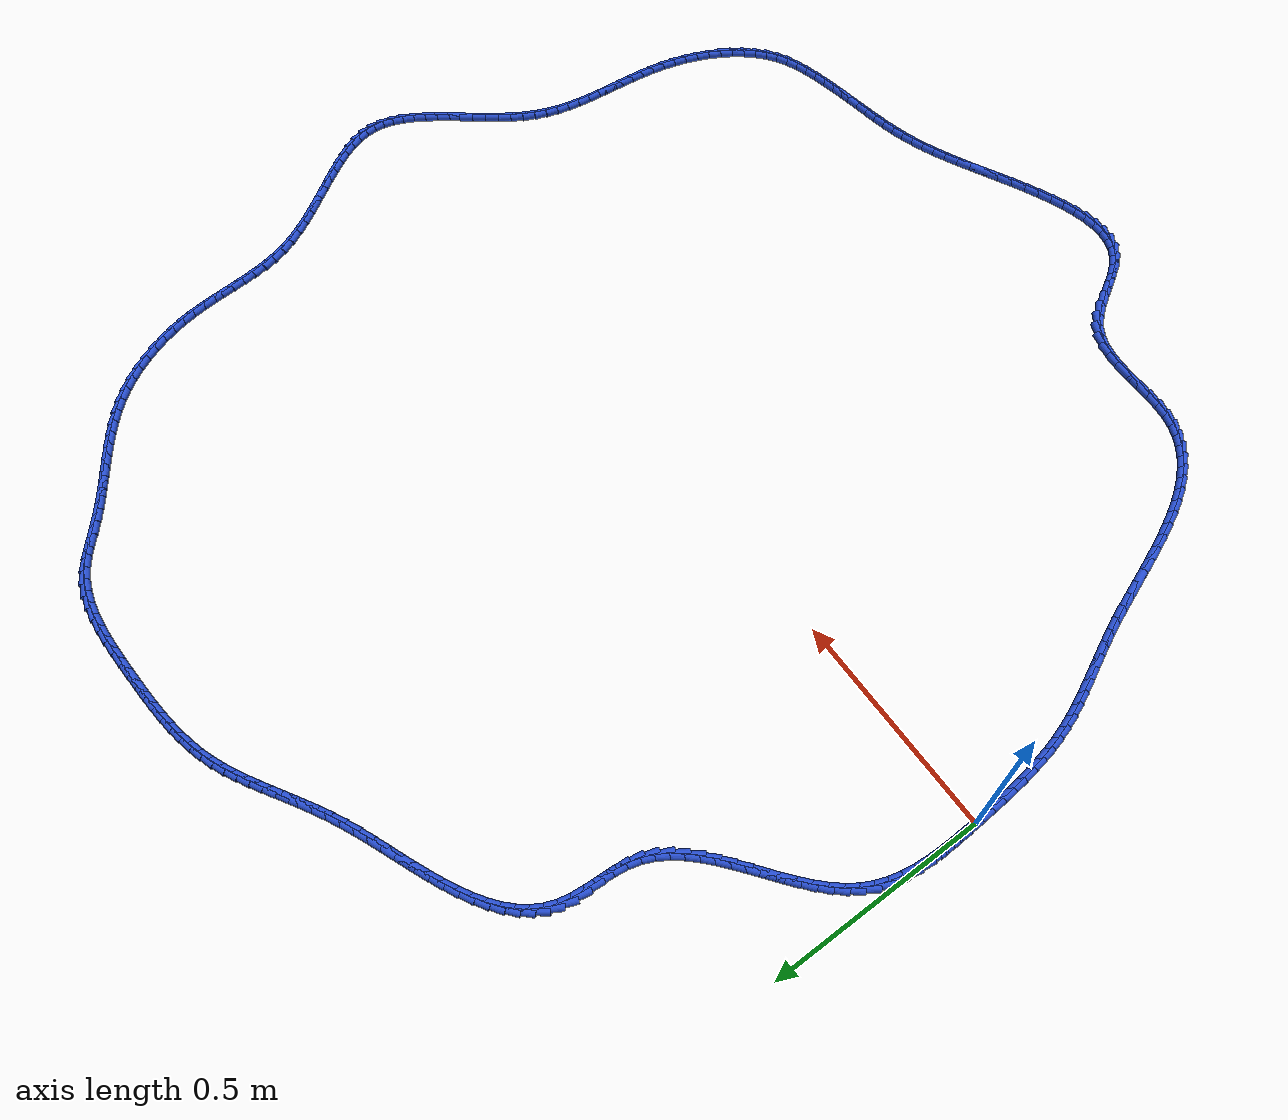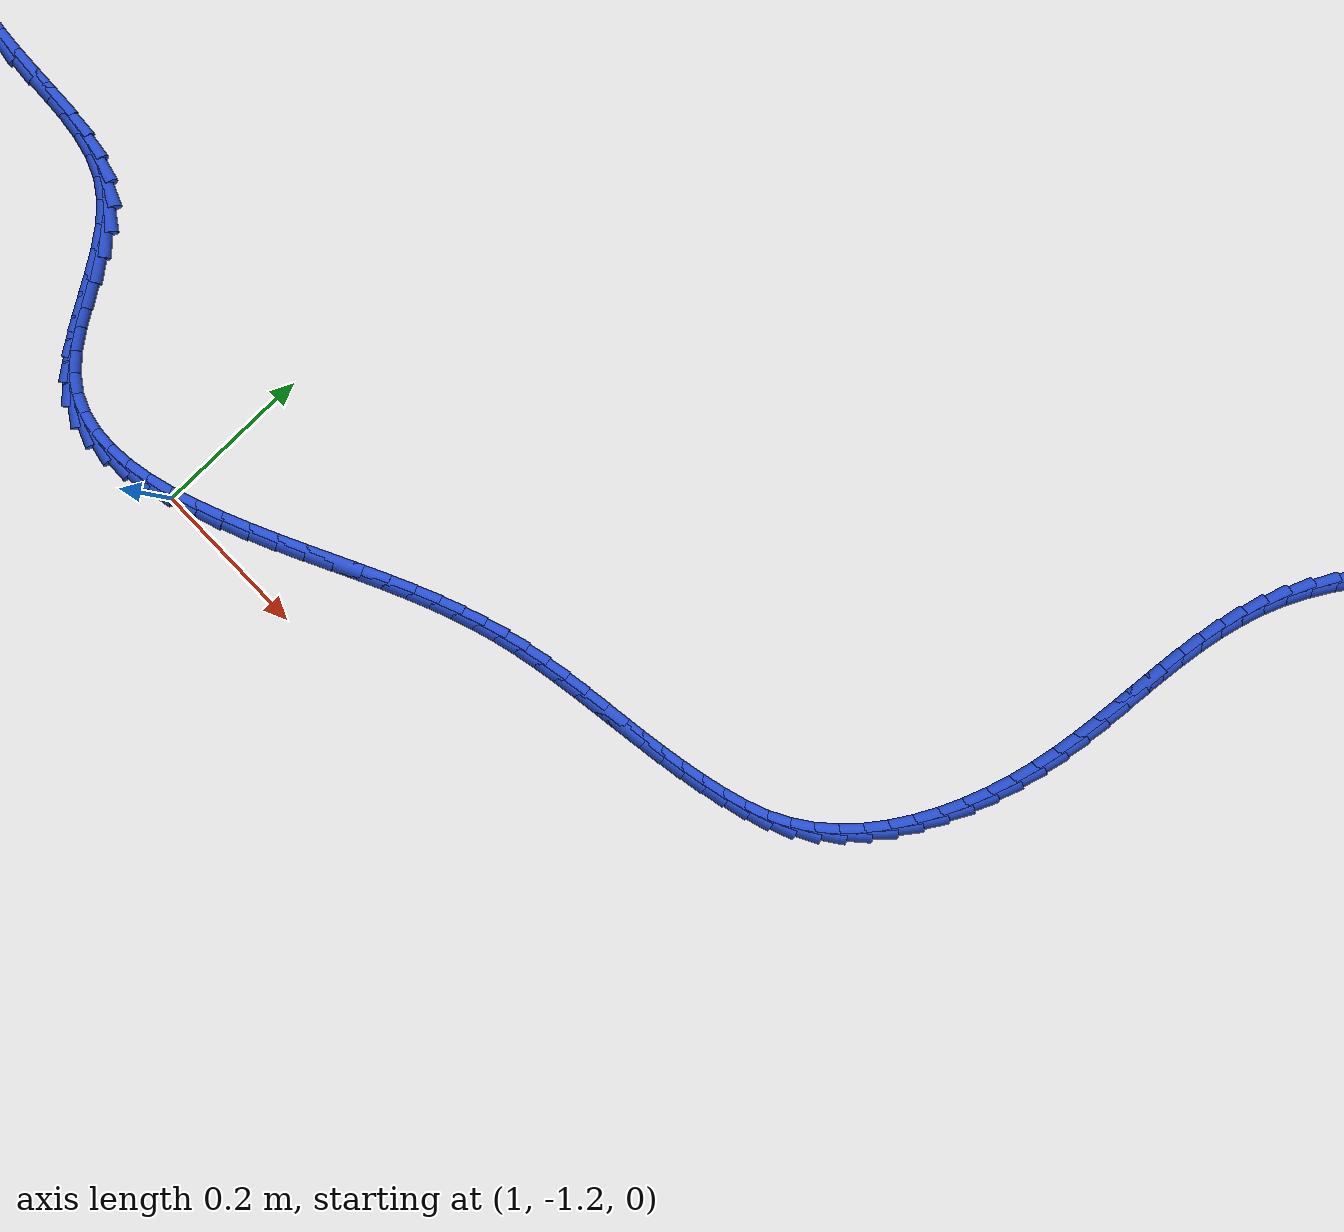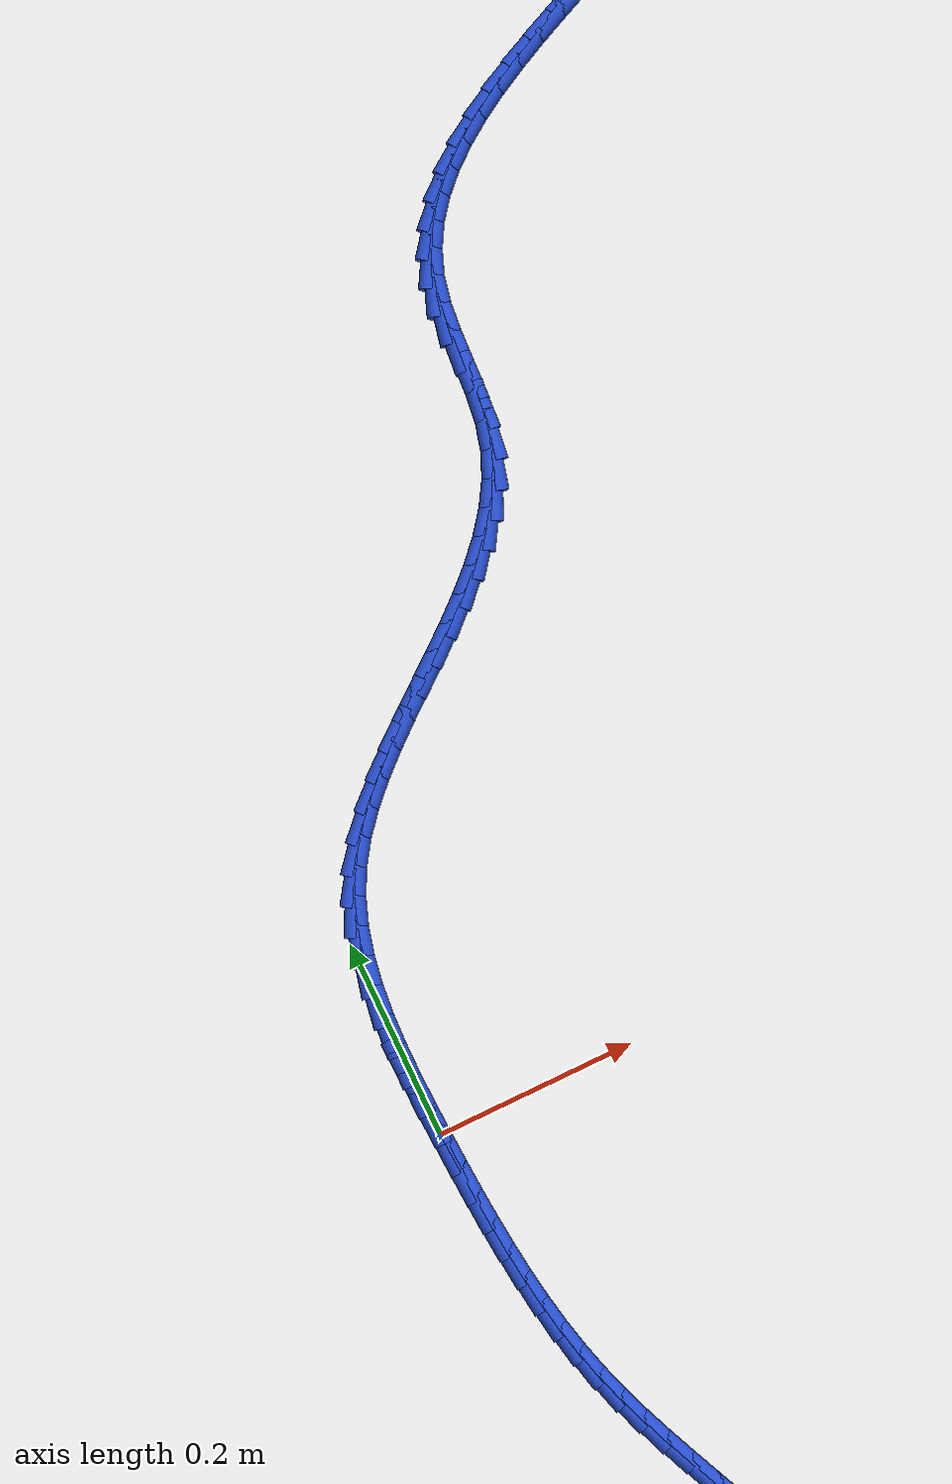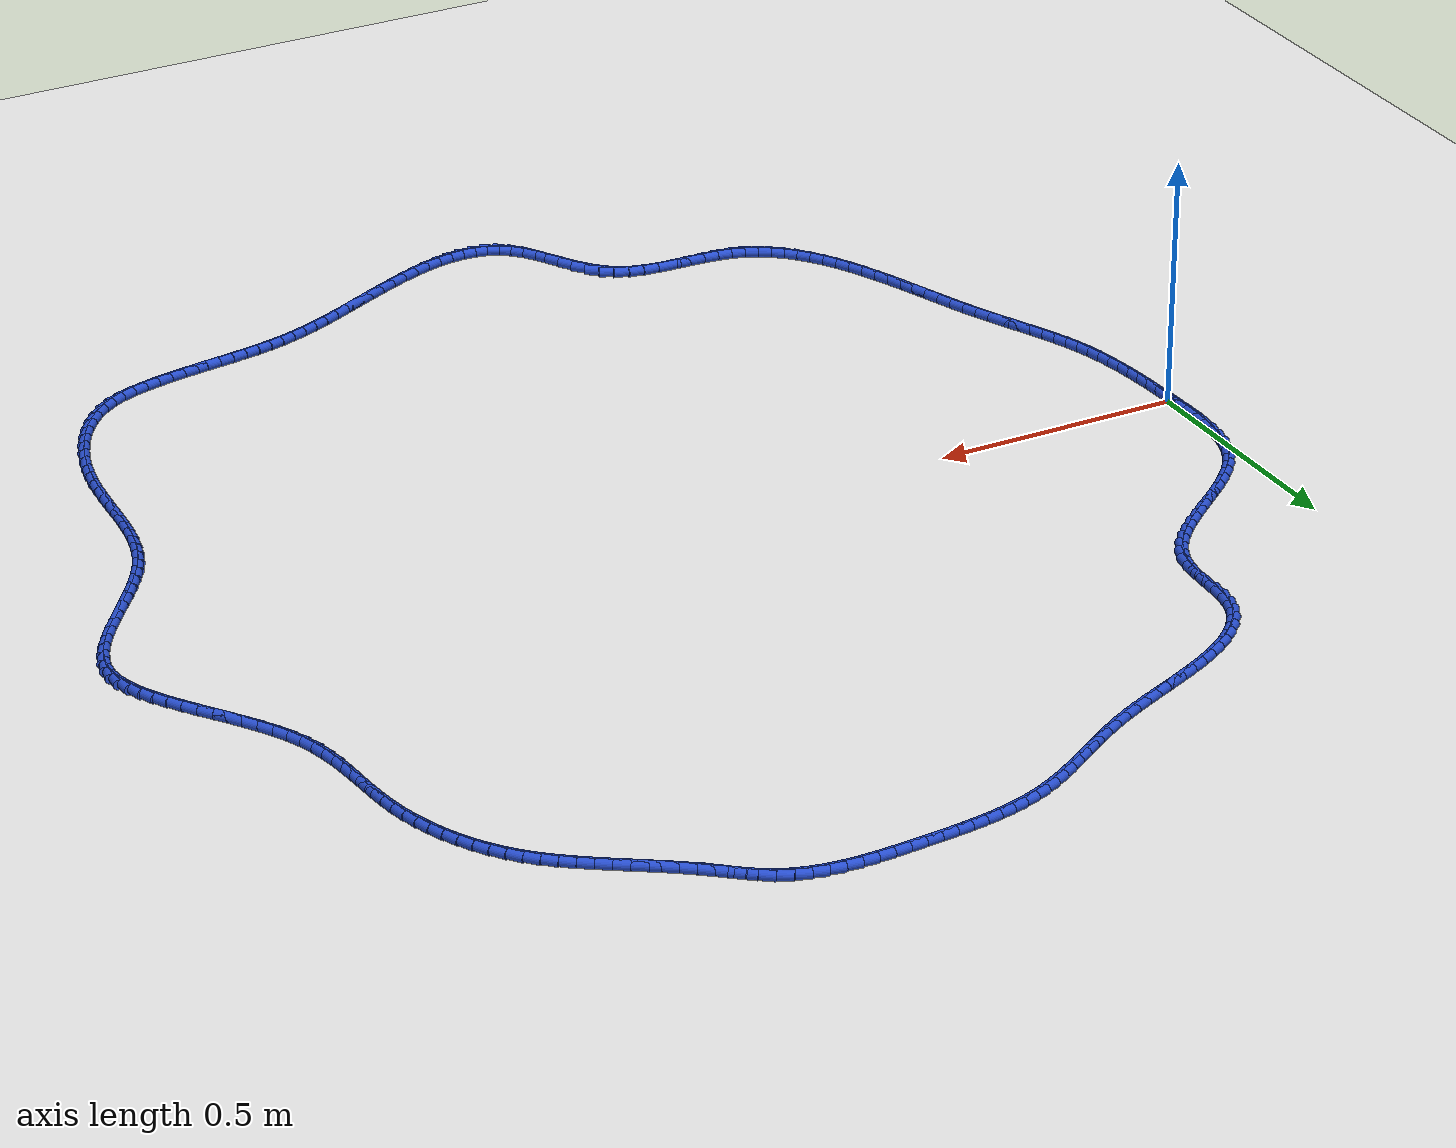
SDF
<sdf version="1.6">
 <world name="default">
  <light name="sun" type="directional">
   <pose>0 0 10 0 -0 0</pose>
   <diffuse>0.8 0.8 0.8 1</diffuse>
   <specular>0.2 0.2 0.2 1</specular>
   <attenuation>
    <range>1000</range>
    <constant>0.9</constant>
    <linear>0.01</linear>
    <quadratic>0.001</quadratic>
   </attenuation>
   <direction>-0.5 0.1 -0.9</direction>
  </light>
  <model name="ground_plane">
   <static>1</static>
   <link name="link">
    <collision name="collision">
     <geometry><plane><normal>0 0 1</normal><size>100 100</size></plane></geometry>
     <surface><friction><ode><mu>100</mu><mu2>50</mu2></ode></friction></surface>
    </collision>
    <visual name="visual">
     <cast_shadows>0</cast_shadows>
     <geometry><plane><normal>0 0 1</normal><size>100 100</size></plane></geometry>
     <material>
      <script><uri>file://media/materials/scripts/gazebo.material</uri><name>Gazebo/WhiteGlow</name></script>
     </material>
    </visual>
   </link>
  </model>
  <gravity>0 0 -9.8</gravity>
  <magnetic_field>6e-06 2.3e-05 -4.2e-05</magnetic_field>
  <atmosphere type="adiabatic"/>
  <physics name="default_physics" default="0" type="ode">
   <max_step_size>0.001</max_step_size>
   <real_time_factor>1</real_time_factor>
   <real_time_update_rate>1000</real_time_update_rate>
  </physics>
  <scene><ambient>0.4 0.4 0.4 1</ambient><background>0.7 0.7 0.7 1</background><shadows>1</shadows></scene>
  <spherical_coordinates>
   <surface_model>EARTH_WGS84</surface_model>
   <latitude_deg>0</latitude_deg>
   <longitude_deg>0</longitude_deg>
   <elevation>0</elevation>
   <heading_deg>0</heading_deg>
  </spherical_coordinates>
  <model name="line">
   <link name="link_0">
    <pose>1.951563910473908e-18 3.469446951953614e-17 0.01 0 1.57 -1.5276882192725305</pose>
    <collision name="collision">
     <geometry><cylinder><radius>0.01</radius><length>0.08</length></cylinder></geometry>
    </collision>
    <visual name="visual">
     <material>
      <script><name>Gazebo/Blue</name><uri>file://media/materials/scripts/gazebo.material</uri></script>
     </material>
     <geometry><cylinder><radius>0.01</radius><length>0.08</length></cylinder></geometry>
    </visual>
   </link>
   <link name="link_1">
    <pose>-0.0013461957831000743 0.031209020171577916 0.01 0 1.57 -1.5441286582476965</pose>
    <collision name="collision">
     <geometry><cylinder><radius>0.01</radius><length>0.08</length></cylinder></geometry>
    </collision>
    <visual name="visual">
     <material>
      <script><name>Gazebo/Blue</name><uri>file://media/materials/scripts/gazebo.material</uri></script>
     </material>
     <geometry><cylinder><radius>0.01</radius><length>0.08</length></cylinder></geometry>
    </visual>
   </link>
   <link name="link_2">
    <pose>-0.002180284611352953 0.06247876137902921 0.01 0 1.57 1.5692639998427684</pose>
    <collision name="collision">
     <geometry><cylinder><radius>0.01</radius><length>0.08</length></cylinder></geometry>
    </collision>
    <visual name="visual">
     <material>
      <script><name>Gazebo/Blue</name><uri>file://media/materials/scripts/gazebo.material</uri></script>
     </material>
     <geometry><cylinder><radius>0.01</radius><length>0.08</length></cylinder></geometry>
    </visual>
   </link>
   <link name="link_3">
    <pose>-0.0021326142913077953 0.09358849463051473 0.01 0 1.57 1.5285460506647996</pose>
    <collision name="collision">
     <geometry><cylinder><radius>0.01</radius><length>0.08</length></cylinder></geometry>
    </collision>
    <visual name="visual">
     <material>
      <script><name>Gazebo/Blue</name><uri>file://media/materials/scripts/gazebo.material</uri></script>
     </material>
     <geometry><cylinder><radius>0.01</radius><length>0.08</length></cylinder></geometry>
    </visual>
   </link>
   <link name="link_4">
    <pose>-0.000833532629513768 0.12431749093419543 0.01 0 1.57 1.4741720181184212</pose>
    <collision name="collision">
     <geometry><cylinder><radius>0.01</radius><length>0.08</length></cylinder></geometry>
    </collision>
    <visual name="visual">
     <material>
      <script><name>Gazebo/Blue</name><uri>file://media/materials/scripts/gazebo.material</uri></script>
     </material>
     <geometry><cylinder><radius>0.01</radius><length>0.08</length></cylinder></geometry>
    </visual>
   </link>
   <link name="link_5">
    <pose>0.0020866125674799613 0.1544450212982322 0.01 0 1.57 1.4047633540465887</pose>
    <collision name="collision">
     <geometry><cylinder><radius>0.01</radius><length>0.08</length></cylinder></geometry>
    </collision>
    <visual name="visual">
     <material>
      <script><name>Gazebo/Blue</name><uri>file://media/materials/scripts/gazebo.material</uri></script>
     </material>
     <geometry><cylinder><radius>0.01</radius><length>0.08</length></cylinder></geometry>
    </visual>
   </link>
   <link name="link_6">
    <pose>0.00699747349312424 0.18375035673078594 0.01 0 1.57 1.3189818500896837</pose>
    <collision name="collision">
     <geometry><cylinder><radius>0.01</radius><length>0.08</length></cylinder></geometry>
    </collision>
    <visual name="visual">
     <material>
      <script><name>Gazebo/Blue</name><uri>file://media/materials/scripts/gazebo.material</uri></script>
     </material>
     <geometry><cylinder><radius>0.01</radius><length>0.08</length></cylinder></geometry>
    </visual>
   </link>
   <link name="link_7">
    <pose>0.014268702340869893 0.21201276824001752 0.01 0 1.57 1.2160350206963748</pose>
    <collision name="collision">
     <geometry><cylinder><radius>0.01</radius><length>0.08</length></cylinder></geometry>
    </collision>
    <visual name="visual">
     <material>
      <script><name>Gazebo/Blue</name><uri>file://media/materials/scripts/gazebo.material</uri></script>
     </material>
     <geometry><cylinder><radius>0.01</radius><length>0.08</length></cylinder></geometry>
    </visual>
   </link>
   <link name="link_8">
    <pose>0.024269951304167765 0.23901152683408775 0.01 0 1.57 1.0964997287381881</pose>
    <collision name="collision">
     <geometry><cylinder><radius>0.01</radius><length>0.08</length></cylinder></geometry>
    </collision>
    <visual name="visual">
     <material>
      <script><name>Gazebo/Blue</name><uri>file://media/materials/scripts/gazebo.material</uri></script>
     </material>
     <geometry><cylinder><radius>0.01</radius><length>0.08</length></cylinder></geometry>
    </visual>
   </link>
   <link name="link_9">
    <pose>0.037369085124948555 0.2645268513051817 0.01 0 1.57 0.9734054817675105</pose>
    <collision name="collision">
     <geometry><cylinder><radius>0.01</radius><length>0.08</length></cylinder></geometry>
    </collision>
    <visual name="visual">
     <material>
      <script><name>Gazebo/Blue</name><uri>file://media/materials/scripts/gazebo.material</uri></script>
     </material>
     <geometry><cylinder><radius>0.01</radius><length>0.08</length></cylinder></geometry>
    </visual>
   </link>
   <link name="link_10">
    <pose>0.053665591186455454 0.288481265716497 0.01 0 1.57 0.8708366883629408</pose>
    <collision name="collision">
     <geometry><cylinder><radius>0.01</radius><length>0.08</length></cylinder></geometry>
    </collision>
    <visual name="visual">
     <material>
      <script><name>Gazebo/Blue</name><uri>file://media/materials/scripts/gazebo.material</uri></script>
     </material>
     <geometry><cylinder><radius>0.01</radius><length>0.08</length></cylinder></geometry>
    </visual>
   </link>
   <link name="link_11">
    <pose>0.07270705285808933 0.3110899374847805 0.01 0 1.57 0.7911955926520953</pose>
    <collision name="collision">
     <geometry><cylinder><radius>0.01</radius><length>0.08</length></cylinder></geometry>
    </collision>
    <visual name="visual">
     <material>
      <script><name>Gazebo/Blue</name><uri>file://media/materials/scripts/gazebo.material</uri></script>
     </material>
     <geometry><cylinder><radius>0.01</radius><length>0.08</length></cylinder></geometry>
    </visual>
   </link>
   <link name="link_12">
    <pose>0.09397314140119684 0.33260404396065973 0.01 0 1.57 0.7327518537921345</pose>
    <collision name="collision">
     <geometry><cylinder><radius>0.01</radius><length>0.08</length></cylinder></geometry>
    </collision>
    <visual name="visual">
     <material>
      <script><name>Gazebo/Blue</name><uri>file://media/materials/scripts/gazebo.material</uri></script>
     </material>
     <geometry><cylinder><radius>0.01</radius><length>0.08</length></cylinder></geometry>
    </visual>
   </link>
   <link name="link_13">
    <pose>0.11694352807712456 0.3532747624947634 0.01 0 1.57 0.693512390965186</pose>
    <collision name="collision">
     <geometry><cylinder><radius>0.01</radius><length>0.08</length></cylinder></geometry>
    </collision>
    <visual name="visual">
     <material>
      <script><name>Gazebo/Blue</name><uri>file://media/materials/scripts/gazebo.material</uri></script>
     </material>
     <geometry><cylinder><radius>0.01</radius><length>0.08</length></cylinder></geometry>
    </visual>
   </link>
   <link name="link_14">
    <pose>0.14109788414721922 0.3733532704377196 0.01 0 1.57 0.6718616469457965</pose>
    <collision name="collision">
     <geometry><cylinder><radius>0.01</radius><length>0.08</length></cylinder></geometry>
    </collision>
    <visual name="visual">
     <material>
      <script><name>Gazebo/Blue</name><uri>file://media/materials/scripts/gazebo.material</uri></script>
     </material>
     <geometry><cylinder><radius>0.01</radius><length>0.08</length></cylinder></geometry>
    </visual>
   </link>
   <link name="link_15">
    <pose>0.16591588087282738 0.39309074514015646 0.01 0 1.57 0.6668396117418598</pose>
    <collision name="collision">
     <geometry><cylinder><radius>0.01</radius><length>0.08</length></cylinder></geometry>
    </collision>
    <visual name="visual">
     <material>
      <script><name>Gazebo/Blue</name><uri>file://media/materials/scripts/gazebo.material</uri></script>
     </material>
     <geometry><cylinder><radius>0.01</radius><length>0.08</length></cylinder></geometry>
    </visual>
   </link>
   <link name="link_16">
    <pose>0.1908771895152958 0.41273836395270225 0.01 0 1.57 0.6782408478617574</pose>
    <collision name="collision">
     <geometry><cylinder><radius>0.01</radius><length>0.08</length></cylinder></geometry>
    </collision>
    <visual name="visual">
     <material>
      <script><name>Gazebo/Blue</name><uri>file://media/materials/scripts/gazebo.material</uri></script>
     </material>
     <geometry><cylinder><radius>0.01</radius><length>0.08</length></cylinder></geometry>
    </visual>
   </link>
   <link name="link_17">
    <pose>0.215461481335971 0.43254730422598514 0.01 0 1.57 0.7066355753539529</pose>
    <collision name="collision">
     <geometry><cylinder><radius>0.01</radius><length>0.08</length></cylinder></geometry>
    </collision>
    <visual name="visual">
     <material>
      <script><name>Gazebo/Blue</name><uri>file://media/materials/scripts/gazebo.material</uri></script>
     </material>
     <geometry><cylinder><radius>0.01</radius><length>0.08</length></cylinder></geometry>
    </visual>
   </link>
   <link name="link_18">
    <pose>0.23914842759619975 0.45276874331063327 0.01 0 1.57 0.7533346251429583</pose>
    <collision name="collision">
     <geometry><cylinder><radius>0.01</radius><length>0.08</length></cylinder></geometry>
    </collision>
    <visual name="visual">
     <material>
      <script><name>Gazebo/Blue</name><uri>file://media/materials/scripts/gazebo.material</uri></script>
     </material>
     <geometry><cylinder><radius>0.01</radius><length>0.08</length></cylinder></geometry>
    </visual>
   </link>
   <link name="link_19">
    <pose>0.2614176995573285 0.4736538585572749 0.01 0 1.57 0.82024416876418</pose>
    <collision name="collision">
     <geometry><cylinder><radius>0.01</radius><length>0.08</length></cylinder></geometry>
    </collision>
    <visual name="visual">
     <material>
      <script><name>Gazebo/Blue</name><uri>file://media/materials/scripts/gazebo.material</uri></script>
     </material>
     <geometry><cylinder><radius>0.01</radius><length>0.08</length></cylinder></geometry>
    </visual>
   </link>
   <link name="link_20">
    <pose>0.28174896848070424 0.4954538273165385 0.01 0 1.57 0.909468541712482</pose>
    <collision name="collision">
     <geometry><cylinder><radius>0.01</radius><length>0.08</length></cylinder></geometry>
    </collision>
    <visual name="visual">
     <material>
      <script><name>Gazebo/Blue</name><uri>file://media/materials/scripts/gazebo.material</uri></script>
     </material>
     <geometry><cylinder><radius>0.01</radius><length>0.08</length></cylinder></geometry>
    </visual>
   </link>
   <link name="link_21">
    <pose>0.2996219056276734 0.5184198269390519 0.01 0 1.57 1.0224432077306291</pose>
    <collision name="collision">
     <geometry><cylinder><radius>0.01</radius><length>0.08</length></cylinder></geometry>
    </collision>
    <visual name="visual">
     <material>
      <script><name>Gazebo/Blue</name><uri>file://media/materials/scripts/gazebo.material</uri></script>
     </material>
     <geometry><cylinder><radius>0.01</radius><length>0.08</length></cylinder></geometry>
    </visual>
   </link>
   <link name="link_22">
    <pose>0.31451618225958256 0.5428030347754433 0.01 0 1.57 1.15845949838063</pose>
    <collision name="collision">
     <geometry><cylinder><radius>0.01</radius><length>0.08</length></cylinder></geometry>
    </collision>
    <visual name="visual">
     <material>
      <script><name>Gazebo/Blue</name><uri>file://media/materials/scripts/gazebo.material</uri></script>
     </material>
     <geometry><cylinder><radius>0.01</radius><length>0.08</length></cylinder></geometry>
    </visual>
   </link>
   <link name="link_23">
    <pose>0.3259114696377784 0.5688546281763411 0.01 0 1.57 1.3119193900481965</pose>
    <collision name="collision">
     <geometry><cylinder><radius>0.01</radius><length>0.08</length></cylinder></geometry>
    </collision>
    <visual name="visual">
     <material>
      <script><name>Gazebo/Blue</name><uri>file://media/materials/scripts/gazebo.material</uri></script>
     </material>
     <geometry><cylinder><radius>0.01</radius><length>0.08</length></cylinder></geometry>
    </visual>
   </link>
   <link name="link_24">
    <pose>0.333314987341844 0.5968114878327897 0.01 0 1.57 1.4413850309598712</pose>
    <collision name="collision">
     <geometry><cylinder><radius>0.01</radius><length>0.08</length></cylinder></geometry>
    </collision>
    <visual name="visual">
     <material>
      <script><name>Gazebo/Blue</name><uri>file://media/materials/scripts/gazebo.material</uri></script>
     </material>
     <geometry><cylinder><radius>0.01</radius><length>0.08</length></cylinder></geometry>
    </visual>
   </link>
   <link name="link_25">
    <pose>0.33716888679877155 0.6264252959477751 0.01 0 1.57 1.5088438475190324</pose>
    <collision name="collision">
     <geometry><cylinder><radius>0.01</radius><length>0.08</length></cylinder></geometry>
    </collision>
    <visual name="visual">
     <material>
      <script><name>Gazebo/Blue</name><uri>file://media/materials/scripts/gazebo.material</uri></script>
     </material>
     <geometry><cylinder><radius>0.01</radius><length>0.08</length></cylinder></geometry>
    </visual>
   </link>
   <link name="link_26">
    <pose>0.3390565280924274 0.6568554854427915 0.01 0 1.57 1.519013222307939</pose>
    <collision name="collision">
     <geometry><cylinder><radius>0.01</radius><length>0.08</length></cylinder></geometry>
    </collision>
    <visual name="visual">
     <material>
      <script><name>Gazebo/Blue</name><uri>file://media/materials/scripts/gazebo.material</uri></script>
     </material>
     <geometry><cylinder><radius>0.01</radius><length>0.08</length></cylinder></geometry>
    </visual>
   </link>
   <link name="link_27">
    <pose>0.34063058971649096 0.6872255152935001 0.01 0 1.57 1.472142739730491</pose>
    <collision name="collision">
     <geometry><cylinder><radius>0.01</radius><length>0.08</length></cylinder></geometry>
    </collision>
    <visual name="visual">
     <material>
      <script><name>Gazebo/Blue</name><uri>file://media/materials/scripts/gazebo.material</uri></script>
     </material>
     <geometry><cylinder><radius>0.01</radius><length>0.08</length></cylinder></geometry>
    </visual>
   </link>
   <link name="link_28">
    <pose>0.3435437501646419 0.7166588444755615 0.01 0 1.57 1.3606958758678895</pose>
    <collision name="collision">
     <geometry><cylinder><radius>0.01</radius><length>0.08</length></cylinder></geometry>
    </collision>
    <visual name="visual">
     <material>
      <script><name>Gazebo/Blue</name><uri>file://media/materials/scripts/gazebo.material</uri></script>
     </material>
     <geometry><cylinder><radius>0.01</radius><length>0.08</length></cylinder></geometry>
    </visual>
   </link>
   <link name="link_29">
    <pose>0.3494352204976636 0.7442862324172754 0.01 0 1.57 1.203485710366328</pose>
    <collision name="collision">
     <geometry><cylinder><radius>0.01</radius><length>0.08</length></cylinder></geometry>
    </collision>
    <visual name="visual">
     <material>
      <script><name>Gazebo/Blue</name><uri>file://media/materials/scripts/gazebo.material</uri></script>
     </material>
     <geometry><cylinder><radius>0.01</radius><length>0.08</length></cylinder></geometry>
    </visual>
   </link>
   <link name="link_30">
    <pose>0.359192857159661 0.7696457343423273 0.01 0 1.57 1.0485325796928393</pose>
    <collision name="collision">
     <geometry><cylinder><radius>0.01</radius><length>0.08</length></cylinder></geometry>
    </collision>
    <visual name="visual">
     <material>
      <script><name>Gazebo/Blue</name><uri>file://media/materials/scripts/gazebo.material</uri></script>
     </material>
     <geometry><cylinder><radius>0.01</radius><length>0.08</length></cylinder></geometry>
    </visual>
   </link>
   <link name="link_31">
    <pose>0.3725713950492419 0.7928896502409886 0.01 0 1.57 0.9077378172759377</pose>
    <collision name="collision">
     <geometry><cylinder><radius>0.01</radius><length>0.08</length></cylinder></geometry>
    </collision>
    <visual name="visual">
     <material>
      <script><name>Gazebo/Blue</name><uri>file://media/materials/scripts/gazebo.material</uri></script>
     </material>
     <geometry><cylinder><radius>0.01</radius><length>0.08</length></cylinder></geometry>
    </visual>
   </link>
   <link name="link_32">
    <pose>0.3892316846892908 0.8142211731314506 0.01 0 1.57 0.7858935331629243</pose>
    <collision name="collision">
     <geometry><cylinder><radius>0.01</radius><length>0.08</length></cylinder></geometry>
    </collision>
    <visual name="visual">
     <material>
      <script><name>Gazebo/Blue</name><uri>file://media/materials/scripts/gazebo.material</uri></script>
     </material>
     <geometry><cylinder><radius>0.01</radius><length>0.08</length></cylinder></geometry>
    </visual>
   </link>
   <link name="link_33">
    <pose>0.40883457660269196 0.8338434960319042 0.01 0 1.57 0.684311383742679</pose>
    <collision name="collision">
     <geometry><cylinder><radius>0.01</radius><length>0.08</length></cylinder></geometry>
    </collision>
    <visual name="visual">
     <material>
      <script><name>Gazebo/Blue</name><uri>file://media/materials/scripts/gazebo.material</uri></script>
     </material>
     <geometry><cylinder><radius>0.01</radius><length>0.08</length></cylinder></geometry>
    </visual>
   </link>
   <link name="link_34">
    <pose>0.43104092131232963 0.851959811960541 0.01 0 1.57 0.6020078966794598</pose>
    <collision name="collision">
     <geometry><cylinder><radius>0.01</radius><length>0.08</length></cylinder></geometry>
    </collision>
    <visual name="visual">
     <material>
      <script><name>Gazebo/Blue</name><uri>file://media/materials/scripts/gazebo.material</uri></script>
     </material>
     <geometry><cylinder><radius>0.01</radius><length>0.08</length></cylinder></geometry>
    </visual>
   </link>
   <link name="link_35">
    <pose>0.4555115693410884 0.8687733139355523 0.01 0 1.57 0.5369693232323316</pose>
    <collision name="collision">
     <geometry><cylinder><radius>0.01</radius><length>0.08</length></cylinder></geometry>
    </collision>
    <visual name="visual">
     <material>
      <script><name>Gazebo/Blue</name><uri>file://media/materials/scripts/gazebo.material</uri></script>
     </material>
     <geometry><cylinder><radius>0.01</radius><length>0.08</length></cylinder></geometry>
    </visual>
   </link>
   <link name="link_36">
    <pose>0.48190737121185256 0.8844871949751293 0.01 0 1.57 0.4869984801135756</pose>
    <collision name="collision">
     <geometry><cylinder><radius>0.01</radius><length>0.08</length></cylinder></geometry>
    </collision>
    <visual name="visual">
     <material>
      <script><name>Gazebo/Blue</name><uri>file://media/materials/scripts/gazebo.material</uri></script>
     </material>
     <geometry><cylinder><radius>0.01</radius><length>0.08</length></cylinder></geometry>
    </visual>
   </link>
   <link name="link_37">
    <pose>0.5098891774475064 0.8993046480974634 0.01 0 1.57 0.45014327879600646</pose>
    <collision name="collision">
     <geometry><cylinder><radius>0.01</radius><length>0.08</length></cylinder></geometry>
    </collision>
    <visual name="visual">
     <material>
      <script><name>Gazebo/Blue</name><uri>file://media/materials/scripts/gazebo.material</uri></script>
     </material>
     <geometry><cylinder><radius>0.01</radius><length>0.08</length></cylinder></geometry>
    </visual>
   </link>
   <link name="link_38">
    <pose>0.5391178385709344 0.913428866320746 0.01 0 1.57 0.42486130963489155</pose>
    <collision name="collision">
     <geometry><cylinder><radius>0.01</radius><length>0.08</length></cylinder></geometry>
    </collision>
    <visual name="visual">
     <material>
      <script><name>Gazebo/Blue</name><uri>file://media/materials/scripts/gazebo.material</uri></script>
     </material>
     <geometry><cylinder><radius>0.01</radius><length>0.08</length></cylinder></geometry>
    </visual>
   </link>
   <link name="link_39">
    <pose>0.5692542051050209 0.9270630426631679 0.01 0 1.57 0.4100550604197094</pose>
    <collision name="collision">
     <geometry><cylinder><radius>0.01</radius><length>0.08</length></cylinder></geometry>
    </collision>
    <visual name="visual">
     <material>
      <script><name>Gazebo/Blue</name><uri>file://media/materials/scripts/gazebo.material</uri></script>
     </material>
     <geometry><cylinder><radius>0.01</radius><length>0.08</length></cylinder></geometry>
    </visual>
   </link>
   <link name="link_40">
    <pose>0.5999591275726504 0.940410370142921 0.01 0 1.57 0.4050584248168017</pose>
    <collision name="collision">
     <geometry><cylinder><radius>0.01</radius><length>0.08</length></cylinder></geometry>
    </collision>
    <visual name="visual">
     <material>
      <script><name>Gazebo/Blue</name><uri>file://media/materials/scripts/gazebo.material</uri></script>
     </material>
     <geometry><cylinder><radius>0.01</radius><length>0.08</length></cylinder></geometry>
    </visual>
   </link>
   <link name="link_41">
    <pose>0.6308934564967071 0.9536740417781961 0.01 0 1.57 0.4096146950289556</pose>
    <collision name="collision">
     <geometry><cylinder><radius>0.01</radius><length>0.08</length></cylinder></geometry>
    </collision>
    <visual name="visual">
     <material>
      <script><name>Gazebo/Blue</name><uri>file://media/materials/scripts/gazebo.material</uri></script>
     </material>
     <geometry><cylinder><radius>0.01</radius><length>0.08</length></cylinder></geometry>
    </visual>
   </link>
   <link name="link_42">
    <pose>0.6617180424000753 0.9670572505871848 0.01 0 1.57 0.42386305473692276</pose>
    <collision name="collision">
     <geometry><cylinder><radius>0.01</radius><length>0.08</length></cylinder></geometry>
    </collision>
    <visual name="visual">
     <material>
      <script><name>Gazebo/Blue</name><uri>file://media/materials/scripts/gazebo.material</uri></script>
     </material>
     <geometry><cylinder><radius>0.01</radius><length>0.08</length></cylinder></geometry>
    </visual>
   </link>
   <link name="link_43">
    <pose>0.6920937358056396 0.9807631895880785 0.01 0 1.57 0.44833794276709543</pose>
    <collision name="collision">
     <geometry><cylinder><radius>0.01</radius><length>0.08</length></cylinder></geometry>
    </collision>
    <visual name="visual">
     <material>
      <script><name>Gazebo/Blue</name><uri>file://media/materials/scripts/gazebo.material</uri></script>
     </material>
     <geometry><cylinder><radius>0.01</radius><length>0.08</length></cylinder></geometry>
    </visual>
   </link>
   <link name="link_44">
    <pose>0.7216813872362844 0.9949950517990682 0.01 0 1.57 0.48269421231455245</pose>
    <collision name="collision">
     <geometry><cylinder><radius>0.01</radius><length>0.08</length></cylinder></geometry>
    </collision>
    <visual name="visual">
     <material>
      <script><name>Gazebo/Blue</name><uri>file://media/materials/scripts/gazebo.material</uri></script>
     </material>
     <geometry><cylinder><radius>0.01</radius><length>0.08</length></cylinder></geometry>
    </visual>
   </link>
   <link name="link_45">
    <pose>0.7501762313350653 1.0099274928182826 0.01 0 1.57 0.5155748872746178</pose>
    <collision name="collision">
     <geometry><cylinder><radius>0.01</radius><length>0.08</length></cylinder></geometry>
    </collision>
    <visual name="visual">
     <material>
      <script><name>Gazebo/Blue</name><uri>file://media/materials/scripts/gazebo.material</uri></script>
     </material>
     <geometry><cylinder><radius>0.01</radius><length>0.08</length></cylinder></geometry>
    </visual>
   </link>
   <link name="link_46">
    <pose>0.7775968659393989 1.0254667899557224 0.01 0 1.57 0.539862307192583</pose>
    <collision name="collision">
     <geometry><cylinder><radius>0.01</radius><length>0.08</length></cylinder></geometry>
    </collision>
    <visual name="visual">
     <material>
      <script><name>Gazebo/Blue</name><uri>file://media/materials/scripts/gazebo.material</uri></script>
     </material>
     <geometry><cylinder><radius>0.01</radius><length>0.08</length></cylinder></geometry>
    </visual>
   </link>
   <link name="link_47">
    <pose>0.8041391830127351 1.0413720736139211 0.01 0 1.57 0.5548456937453472</pose>
    <collision name="collision">
     <geometry><cylinder><radius>0.01</radius><length>0.08</length></cylinder></geometry>
    </collision>
    <visual name="visual">
     <material>
      <script><name>Gazebo/Blue</name><uri>file://media/materials/scripts/gazebo.material</uri></script>
     </material>
     <geometry><cylinder><radius>0.01</radius><length>0.08</length></cylinder></geometry>
    </visual>
   </link>
   <link name="link_48">
    <pose>0.8300008945655305 1.0574009636304842 0.01 0 1.57 0.5599682646833017</pose>
    <collision name="collision">
     <geometry><cylinder><radius>0.01</radius><length>0.08</length></cylinder></geometry>
    </collision>
    <visual name="visual">
     <material>
      <script><name>Gazebo/Blue</name><uri>file://media/materials/scripts/gazebo.material</uri></script>
     </material>
     <geometry><cylinder><radius>0.01</radius><length>0.08</length></cylinder></geometry>
    </visual>
   </link>
   <link name="link_49">
    <pose>0.8553797126082417 1.0733110798430154 0.01 0 1.57 0.5547339546606506</pose>
    <collision name="collision">
     <geometry><cylinder><radius>0.01</radius><length>0.08</length></cylinder></geometry>
    </collision>
    <visual name="visual">
     <material>
      <script><name>Gazebo/Blue</name><uri>file://media/materials/scripts/gazebo.material</uri></script>
     </material>
     <geometry><cylinder><radius>0.01</radius><length>0.08</length></cylinder></geometry>
    </visual>
   </link>
   <link name="link_50">
    <pose>0.880473349151326 1.0888600420891215 0.01 0 1.57 0.5387042755099455</pose>
    <collision name="collision">
     <geometry><cylinder><radius>0.01</radius><length>0.08</length></cylinder></geometry>
    </collision>
    <visual name="visual">
     <material>
      <script><name>Gazebo/Blue</name><uri>file://media/materials/scripts/gazebo.material</uri></script>
     </material>
     <geometry><cylinder><radius>0.01</radius><length>0.08</length></cylinder></geometry>
    </visual>
   </link>
   <link name="link_51">
    <pose>0.9054795162052399 1.1038054702064057 0.01 0 1.57 0.5115280743949868</pose>
    <collision name="collision">
     <geometry><cylinder><radius>0.01</radius><length>0.08</length></cylinder></geometry>
    </collision>
    <visual name="visual">
     <material>
      <script><name>Gazebo/Blue</name><uri>file://media/materials/scripts/gazebo.material</uri></script>
     </material>
     <geometry><cylinder><radius>0.01</radius><length>0.08</length></cylinder></geometry>
    </visual>
   </link>
   <link name="link_52">
    <pose>0.9305959257804407 1.1179049840324746 0.01 0 1.57 0.4730127459231541</pose>
    <collision name="collision">
     <geometry><cylinder><radius>0.01</radius><length>0.08</length></cylinder></geometry>
    </collision>
    <visual name="visual">
     <material>
      <script><name>Gazebo/Blue</name><uri>file://media/materials/scripts/gazebo.material</uri></script>
     </material>
     <geometry><cylinder><radius>0.01</radius><length>0.08</length></cylinder></geometry>
    </visual>
   </link>
   <link name="link_53">
    <pose>0.9560202898873851 1.1309162034049327 0.01 0 1.57 0.4232397036403707</pose>
    <collision name="collision">
     <geometry><cylinder><radius>0.01</radius><length>0.08</length></cylinder></geometry>
    </collision>
    <visual name="visual">
     <material>
      <script><name>Gazebo/Blue</name><uri>file://media/materials/scripts/gazebo.material</uri></script>
     </material>
     <geometry><cylinder><radius>0.01</radius><length>0.08</length></cylinder></geometry>
    </visual>
   </link>
   <link name="link_54">
    <pose>0.9819503205365303 1.142596748161385 0.01 0 1.57 0.3629879177470212</pose>
    <collision name="collision">
     <geometry><cylinder><radius>0.01</radius><length>0.08</length></cylinder></geometry>
    </collision>
    <visual name="visual">
     <material>
      <script><name>Gazebo/Blue</name><uri>file://media/materials/scripts/gazebo.material</uri></script>
     </material>
     <geometry><cylinder><radius>0.01</radius><length>0.08</length></cylinder></geometry>
    </visual>
   </link>
   <link name="link_55">
    <pose>1.0085794972926763 1.152710987377695 0.01 0 1.57 0.3008922405248509</pose>
    <collision name="collision">
     <geometry><cylinder><radius>0.01</radius><length>0.08</length></cylinder></geometry>
    </collision>
    <visual name="visual">
     <material>
      <script><name>Gazebo/Blue</name><uri>file://media/materials/scripts/gazebo.material</uri></script>
     </material>
     <geometry><cylinder><radius>0.01</radius><length>0.08</length></cylinder></geometry>
    </visual>
   </link>
   <link name="link_56">
    <pose>1.0359815586094387 1.1612142344097363 0.01 0 1.57 0.2460496576232189</pose>
    <collision name="collision">
     <geometry><cylinder><radius>0.01</radius><length>0.08</length></cylinder></geometry>
    </collision>
    <visual name="visual">
     <material>
      <script><name>Gazebo/Blue</name><uri>file://media/materials/scripts/gazebo.material</uri></script>
     </material>
     <geometry><cylinder><radius>0.01</radius><length>0.08</length></cylinder></geometry>
    </visual>
   </link>
   <link name="link_57">
    <pose>1.0640965561212292 1.1682749853138592 0.01 0 1.57 0.19892541229311164</pose>
    <collision name="collision">
     <geometry><cylinder><radius>0.01</radius><length>0.08</length></cylinder></geometry>
    </collision>
    <visual name="visual">
     <material>
      <script><name>Gazebo/Blue</name><uri>file://media/materials/scripts/gazebo.material</uri></script>
     </material>
     <geometry><cylinder><radius>0.01</radius><length>0.08</length></cylinder></geometry>
    </visual>
   </link>
   <link name="link_58">
    <pose>1.092857509259093 1.1740729499976577 0.01 0 1.57 0.15933644931017643</pose>
    <collision name="collision">
     <geometry><cylinder><radius>0.01</radius><length>0.08</length></cylinder></geometry>
    </collision>
    <visual name="visual">
     <material>
      <script><name>Gazebo/Blue</name><uri>file://media/materials/scripts/gazebo.material</uri></script>
     </material>
     <geometry><cylinder><radius>0.01</radius><length>0.08</length></cylinder></geometry>
    </visual>
   </link>
   <link name="link_59">
    <pose>1.1221974374540755 1.1787878383687243 0.01 0 1.57 0.12699382622252442</pose>
    <collision name="collision">
     <geometry><cylinder><radius>0.01</radius><length>0.08</length></cylinder></geometry>
    </collision>
    <visual name="visual">
     <material>
      <script><name>Gazebo/Blue</name><uri>file://media/materials/scripts/gazebo.material</uri></script>
     </material>
     <geometry><cylinder><radius>0.01</radius><length>0.08</length></cylinder></geometry>
    </visual>
   </link>
   <link name="link_60">
    <pose>1.1520493601372221 1.1825993603346534 0.01 0 1.57 0.10156933419751353</pose>
    <collision name="collision">
     <geometry><cylinder><radius>0.01</radius><length>0.08</length></cylinder></geometry>
    </collision>
    <visual name="visual">
     <material>
      <script><name>Gazebo/Blue</name><uri>file://media/materials/scripts/gazebo.material</uri></script>
     </material>
     <geometry><cylinder><radius>0.01</radius><length>0.08</length></cylinder></geometry>
    </visual>
   </link>
   <link name="link_61">
    <pose>1.182346296739578 1.1856872258030386 0.01 0 1.57 0.08274207911694119</pose>
    <collision name="collision">
     <geometry><cylinder><radius>0.01</radius><length>0.08</length></cylinder></geometry>
    </collision>
    <visual name="visual">
     <material>
      <script><name>Gazebo/Blue</name><uri>file://media/materials/scripts/gazebo.material</uri></script>
     </material>
     <geometry><cylinder><radius>0.01</radius><length>0.08</length></cylinder></geometry>
    </visual>
   </link>
   <link name="link_62">
    <pose>1.2130212666921885 1.1882311446814733 0.01 0 1.57 0.07022836141062268</pose>
    <collision name="collision">
     <geometry><cylinder><radius>0.01</radius><length>0.08</length></cylinder></geometry>
    </collision>
    <visual name="visual">
     <material>
      <script><name>Gazebo/Blue</name><uri>file://media/materials/scripts/gazebo.material</uri></script>
     </material>
     <geometry><cylinder><radius>0.01</radius><length>0.08</length></cylinder></geometry>
    </visual>
   </link>
   <link name="link_63">
    <pose>1.2440072894260994 1.1904108268775508 0.01 0 1.57 0.06299139876935778</pose>
    <collision name="collision">
     <geometry><cylinder><radius>0.01</radius><length>0.08</length></cylinder></geometry>
    </collision>
    <visual name="visual">
     <material>
      <script><name>Gazebo/Blue</name><uri>file://media/materials/scripts/gazebo.material</uri></script>
     </material>
     <geometry><cylinder><radius>0.01</radius><length>0.08</length></cylinder></geometry>
    </visual>
   </link>
   <link name="link_64">
    <pose>1.275231124897852 1.1923802654940532 0.01 0 1.57 0.05062744018367149</pose>
    <collision name="collision">
     <geometry><cylinder><radius>0.01</radius><length>0.08</length></cylinder></geometry>
    </collision>
    <visual name="visual">
     <material>
      <script><name>Gazebo/Blue</name><uri>file://media/materials/scripts/gazebo.material</uri></script>
     </material>
     <geometry><cylinder><radius>0.01</radius><length>0.08</length></cylinder></geometry>
    </visual>
   </link>
   <link name="link_65">
    <pose>1.3065400034953691 1.1939667095289708 0.01 0 1.57 0.025835764297099696</pose>
    <collision name="collision">
     <geometry><cylinder><radius>0.01</radius><length>0.08</length></cylinder></geometry>
    </collision>
    <visual name="visual">
     <material>
      <script><name>Gazebo/Blue</name><uri>file://media/materials/scripts/gazebo.material</uri></script>
     </material>
     <geometry><cylinder><radius>0.01</radius><length>0.08</length></cylinder></geometry>
    </visual>
   </link>
   <link name="link_66">
    <pose>1.337726440785607 1.1947726142902884 0.01 0 1.57 -0.012204947464806616</pose>
    <collision name="collision">
     <geometry><cylinder><radius>0.01</radius><length>0.08</length></cylinder></geometry>
    </collision>
    <visual name="visual">
     <material>
      <script><name>Gazebo/Blue</name><uri>file://media/materials/scripts/gazebo.material</uri></script>
     </material>
     <geometry><cylinder><radius>0.01</radius><length>0.08</length></cylinder></geometry>
    </visual>
   </link>
   <link name="link_67">
    <pose>1.3685818744518432 1.1943960066432842 0.01 0 1.57 -0.06459866417769501</pose>
    <collision name="collision">
     <geometry><cylinder><radius>0.01</radius><length>0.08</length></cylinder></geometry>
    </collision>
    <visual name="visual">
     <material>
      <script><name>Gazebo/Blue</name><uri>file://media/materials/scripts/gazebo.material</uri></script>
     </material>
     <geometry><cylinder><radius>0.01</radius><length>0.08</length></cylinder></geometry>
    </visual>
   </link>
   <link name="link_68">
    <pose>1.3988977421773545 1.1924349134532353 0.01 0 1.57 -0.132723878665268</pose>
    <collision name="collision">
     <geometry><cylinder><radius>0.01</radius><length>0.08</length></cylinder></geometry>
    </collision>
    <visual name="visual">
     <material>
      <script><name>Gazebo/Blue</name><uri>file://media/materials/scripts/gazebo.material</uri></script>
     </material>
     <geometry><cylinder><radius>0.01</radius><length>0.08</length></cylinder></geometry>
    </visual>
   </link>
   <link name="link_69">
    <pose>1.428465481645419 1.18848736158542 0.01 0 1.57 -0.21793517233601017</pose>
    <collision name="collision">
     <geometry><cylinder><radius>0.01</radius><length>0.08</length></cylinder></geometry>
    </collision>
    <visual name="visual">
     <material>
      <script><name>Gazebo/Blue</name><uri>file://media/materials/scripts/gazebo.material</uri></script>
     </material>
     <geometry><cylinder><radius>0.01</radius><length>0.08</length></cylinder></geometry>
    </visual>
   </link>
   <link name="link_70">
    <pose>1.4570765305393123 1.1821513779051147 0.01 0 1.57 -0.32102206809185646</pose>
    <collision name="collision">
     <geometry><cylinder><radius>0.01</radius><length>0.08</length></cylinder></geometry>
    </collision>
    <visual name="visual">
     <material>
      <script><name>Gazebo/Blue</name><uri>file://media/materials/scripts/gazebo.material</uri></script>
     </material>
     <geometry><cylinder><radius>0.01</radius><length>0.08</length></cylinder></geometry>
    </visual>
   </link>
   <link name="link_71">
    <pose>1.4845223265423124 1.1730249892775981 0.01 0 1.57 -0.44139892792805374</pose>
    <collision name="collision">
     <geometry><cylinder><radius>0.01</radius><length>0.08</length></cylinder></geometry>
    </collision>
    <visual name="visual">
     <material>
      <script><name>Gazebo/Blue</name><uri>file://media/materials/scripts/gazebo.material</uri></script>
     </material>
     <geometry><cylinder><radius>0.01</radius><length>0.08</length></cylinder></geometry>
    </visual>
   </link>
   <link name="link_72">
    <pose>1.5105943073376953 1.160706222568147 0.01 0 1.57 -0.5657553439380983</pose>
    <collision name="collision">
     <geometry><cylinder><radius>0.01</radius><length>0.08</length></cylinder></geometry>
    </collision>
    <visual name="visual">
     <material>
      <script><name>Gazebo/Blue</name><uri>file://media/materials/scripts/gazebo.material</uri></script>
     </material>
     <geometry><cylinder><radius>0.01</radius><length>0.08</length></cylinder></geometry>
    </visual>
   </link>
   <link name="link_73">
    <pose>1.5352231057080645 1.145067028423507 0.01 0 1.57 -0.649163051151366</pose>
    <collision name="collision">
     <geometry><cylinder><radius>0.01</radius><length>0.08</length></cylinder></geometry>
    </collision>
    <visual name="visual">
     <material>
      <script><name>Gazebo/Blue</name><uri>file://media/materials/scripts/gazebo.material</uri></script>
     </material>
     <geometry><cylinder><radius>0.01</radius><length>0.08</length></cylinder></geometry>
    </visual>
   </link>
   <link name="link_74">
    <pose>1.558905991958142 1.127094450575827 0.01 0 1.57 -0.6833527396289902</pose>
    <collision name="collision">
     <geometry><cylinder><radius>0.01</radius><length>0.08</length></cylinder></geometry>
    </collision>
    <visual name="visual">
     <material>
      <script><name>Gazebo/Blue</name><uri>file://media/materials/scripts/gazebo.material</uri></script>
     </material>
     <geometry><cylinder><radius>0.01</radius><length>0.08</length></cylinder></geometry>
    </visual>
   </link>
   <link name="link_75">
    <pose>1.58228440352493 1.1080592410647276 0.01 0 1.57 -0.6712929177075629</pose>
    <collision name="collision">
     <geometry><cylinder><radius>0.01</radius><length>0.08</length></cylinder></geometry>
    </collision>
    <visual name="visual">
     <material>
      <script><name>Gazebo/Blue</name><uri>file://media/materials/scripts/gazebo.material</uri></script>
     </material>
     <geometry><cylinder><radius>0.01</radius><length>0.08</length></cylinder></geometry>
    </visual>
   </link>
   <link name="link_76">
    <pose>1.605995318118645 1.089224220624254 0.01 0 1.57 -0.633973117105814</pose>
    <collision name="collision">
     <geometry><cylinder><radius>0.01</radius><length>0.08</length></cylinder></geometry>
    </collision>
    <visual name="visual">
     <material>
      <script><name>Gazebo/Blue</name><uri>file://media/materials/scripts/gazebo.material</uri></script>
     </material>
     <geometry><cylinder><radius>0.01</radius><length>0.08</length></cylinder></geometry>
    </visual>
   </link>
   <link name="link_77">
    <pose>1.6303680120488673 1.071304984652881 0.01 0 1.57 -0.6046618642572128</pose>
    <collision name="collision">
     <geometry><cylinder><radius>0.01</radius><length>0.08</length></cylinder></geometry>
    </collision>
    <visual name="visual">
     <material>
      <script><name>Gazebo/Blue</name><uri>file://media/materials/scripts/gazebo.material</uri></script>
     </material>
     <geometry><cylinder><radius>0.01</radius><length>0.08</length></cylinder></geometry>
    </visual>
   </link>
   <link name="link_78">
    <pose>1.6552302050139303 1.0541251453331166 0.01 0 1.57 -0.5864422495113113</pose>
    <collision name="collision">
     <geometry><cylinder><radius>0.01</radius><length>0.08</length></cylinder></geometry>
    </collision>
    <visual name="visual">
     <material>
      <script><name>Gazebo/Blue</name><uri>file://media/materials/scripts/gazebo.material</uri></script>
     </material>
     <geometry><cylinder><radius>0.01</radius><length>0.08</length></cylinder></geometry>
    </visual>
   </link>
   <link name="link_79">
    <pose>1.6803634605193594 1.0374262292994503 0.01 0 1.57 -0.5793182789395411</pose>
    <collision name="collision">
     <geometry><cylinder><radius>0.01</radius><length>0.08</length></cylinder></geometry>
    </collision>
    <visual name="visual">
     <material>
      <script><name>Gazebo/Blue</name><uri>file://media/materials/scripts/gazebo.material</uri></script>
     </material>
     <geometry><cylinder><radius>0.01</radius><length>0.08</length></cylinder></geometry>
    </visual>
   </link>
   <link name="link_80">
    <pose>1.7055493420706824 1.0209497631863726 0.01 0 1.57 -0.5833519210986355</pose>
    <collision name="collision">
     <geometry><cylinder><radius>0.01</radius><length>0.08</length></cylinder></geometry>
    </collision>
    <visual name="visual">
     <material>
      <script><name>Gazebo/Blue</name><uri>file://media/materials/scripts/gazebo.material</uri></script>
     </material>
     <geometry><cylinder><radius>0.01</radius><length>0.08</length></cylinder></geometry>
    </visual>
   </link>
   <link name="link_81">
    <pose>1.7305694131734253 1.0044372736283724 0.01 0 1.57 -0.5986913272170409</pose>
    <collision name="collision">
     <geometry><cylinder><radius>0.01</radius><length>0.08</length></cylinder></geometry>
    </collision>
    <visual name="visual">
     <material>
      <script><name>Gazebo/Blue</name><uri>file://media/materials/scripts/gazebo.material</uri></script>
     </material>
     <geometry><cylinder><radius>0.01</radius><length>0.08</length></cylinder></geometry>
    </visual>
   </link>
   <link name="link_82">
    <pose>1.7552052373331144 0.9876302872599396 0.01 0 1.57 -0.6255585480275918</pose>
    <collision name="collision">
     <geometry><cylinder><radius>0.01</radius><length>0.08</length></cylinder></geometry>
    </collision>
    <visual name="visual">
     <material>
      <script><name>Gazebo/Blue</name><uri>file://media/materials/scripts/gazebo.material</uri></script>
     </material>
     <geometry><cylinder><radius>0.01</radius><length>0.08</length></cylinder></geometry>
    </visual>
   </link>
   <link name="link_83">
    <pose>1.7792383780552772 0.9702703307155647 0.01 0 1.57 -0.6641923107368658</pose>
    <collision name="collision">
     <geometry><cylinder><radius>0.01</radius><length>0.08</length></cylinder></geometry>
    </collision>
    <visual name="visual">
     <material>
      <script><name>Gazebo/Blue</name><uri>file://media/materials/scripts/gazebo.material</uri></script>
     </material>
     <geometry><cylinder><radius>0.01</radius><length>0.08</length></cylinder></geometry>
    </visual>
   </link>
   <link name="link_84">
    <pose>1.802450398845439 0.9520989306297366 0.01 0 1.57 -0.7147388923626082</pose>
    <collision name="collision">
     <geometry><cylinder><radius>0.01</radius><length>0.08</length></cylinder></geometry>
    </collision>
    <visual name="visual">
     <material>
      <script><name>Gazebo/Blue</name><uri>file://media/materials/scripts/gazebo.material</uri></script>
     </material>
     <geometry><cylinder><radius>0.01</radius><length>0.08</length></cylinder></geometry>
    </visual>
   </link>
   <link name="link_85">
    <pose>1.8246228632091277 0.9328576136369453 0.01 0 1.57 -0.777087615831865</pose>
    <collision name="collision">
     <geometry><cylinder><radius>0.01</radius><length>0.08</length></cylinder></geometry>
    </collision>
    <visual name="visual">
     <material>
      <script><name>Gazebo/Blue</name><uri>file://media/materials/scripts/gazebo.material</uri></script>
     </material>
     <geometry><cylinder><radius>0.01</radius><length>0.08</length></cylinder></geometry>
    </visual>
   </link>
   <link name="link_86">
    <pose>1.8455373346518695 0.9122879063716811 0.01 0 1.57 -0.8500505865526808</pose>
    <collision name="collision">
     <geometry><cylinder><radius>0.01</radius><length>0.08</length></cylinder></geometry>
    </collision>
    <visual name="visual">
     <material>
      <script><name>Gazebo/Blue</name><uri>file://media/materials/scripts/gazebo.material</uri></script>
     </material>
     <geometry><cylinder><radius>0.01</radius><length>0.08</length></cylinder></geometry>
    </visual>
   </link>
   <link name="link_87">
    <pose>1.8649835134855937 0.8901494263133186 0.01 0 1.57 -0.9246068376021098</pose>
    <collision name="collision">
     <geometry><cylinder><radius>0.01</radius><length>0.08</length></cylinder></geometry>
    </collision>
    <visual name="visual">
     <material>
      <script><name>Gazebo/Blue</name><uri>file://media/materials/scripts/gazebo.material</uri></script>
     </material>
     <geometry><cylinder><radius>0.01</radius><length>0.08</length></cylinder></geometry>
    </visual>
   </link>
   <link name="link_88">
    <pose>1.8828609069785371 0.8664459285691141 0.01 0 1.57 -0.9950174953947333</pose>
    <collision name="collision">
     <geometry><cylinder><radius>0.01</radius><length>0.08</length></cylinder></geometry>
    </collision>
    <visual name="visual">
     <material>
      <script><name>Gazebo/Blue</name><uri>file://media/materials/scripts/gazebo.material</uri></script>
     </material>
     <geometry><cylinder><radius>0.01</radius><length>0.08</length></cylinder></geometry>
    </visual>
   </link>
   <link name="link_89">
    <pose>1.899147831712147 0.841356387735412 0.01 0 1.57 -1.061683226617974</pose>
    <collision name="collision">
     <geometry><cylinder><radius>0.01</radius><length>0.08</length></cylinder></geometry>
    </collision>
    <visual name="visual">
     <material>
      <script><name>Gazebo/Blue</name><uri>file://media/materials/scripts/gazebo.material</uri></script>
     </material>
     <geometry><cylinder><radius>0.01</radius><length>0.08</length></cylinder></geometry>
    </visual>
   </link>
   <link name="link_90">
    <pose>1.9138243269385748 0.8150636084822941 0.01 0 1.57 -1.1251895767879638</pose>
    <collision name="collision">
     <geometry><cylinder><radius>0.01</radius><length>0.08</length></cylinder></geometry>
    </collision>
    <visual name="visual">
     <material>
      <script><name>Gazebo/Blue</name><uri>file://media/materials/scripts/gazebo.material</uri></script>
     </material>
     <geometry><cylinder><radius>0.01</radius><length>0.08</length></cylinder></geometry>
    </visual>
   </link>
   <link name="link_91">
    <pose>1.9268704319099739 0.7877503954798423 0.01 0 1.57 -1.1861499341707493</pose>
    <collision name="collision">
     <geometry><cylinder><radius>0.01</radius><length>0.08</length></cylinder></geometry>
    </collision>
    <visual name="visual">
     <material>
      <script><name>Gazebo/Blue</name><uri>file://media/materials/scripts/gazebo.material</uri></script>
     </material>
     <geometry><cylinder><radius>0.01</radius><length>0.08</length></cylinder></geometry>
    </visual>
   </link>
   <link name="link_92">
    <pose>1.9382661858784949 0.7595995533981376 0.01 0 1.57 -1.245190468543144</pose>
    <collision name="collision">
     <geometry><cylinder><radius>0.01</radius><length>0.08</length></cylinder></geometry>
    </collision>
    <visual name="visual">
     <material>
      <script><name>Gazebo/Blue</name><uri>file://media/materials/scripts/gazebo.material</uri></script>
     </material>
     <geometry><cylinder><radius>0.01</radius><length>0.08</length></cylinder></geometry>
    </visual>
   </link>
   <link name="link_93">
    <pose>1.9479916280962903 0.7307938869072612 0.01 0 1.57 -1.3029444172997642</pose>
    <collision name="collision">
     <geometry><cylinder><radius>0.01</radius><length>0.08</length></cylinder></geometry>
    </collision>
    <visual name="visual">
     <material>
      <script><name>Gazebo/Blue</name><uri>file://media/materials/scripts/gazebo.material</uri></script>
     </material>
     <geometry><cylinder><radius>0.01</radius><length>0.08</length></cylinder></geometry>
    </visual>
   </link>
   <link name="link_94">
    <pose>1.9560267978155121 0.7015162006772956 0.01 0 1.57 -1.3600526529412829</pose>
    <collision name="collision">
     <geometry><cylinder><radius>0.01</radius><length>0.08</length></cylinder></geometry>
    </collision>
    <visual name="visual">
     <material>
      <script><name>Gazebo/Blue</name><uri>file://media/materials/scripts/gazebo.material</uri></script>
     </material>
     <geometry><cylinder><radius>0.01</radius><length>0.08</length></cylinder></geometry>
    </visual>
   </link>
   <link name="link_95">
    <pose>1.9623517509806503 0.6719492953800116 0.01 0 1.57 -1.4138890516357348</pose>
    <collision name="collision">
     <geometry><cylinder><radius>0.01</radius><length>0.08</length></cylinder></geometry>
    </collision>
    <visual name="visual">
     <material>
      <script><name>Gazebo/Blue</name><uri>file://media/materials/scripts/gazebo.material</uri></script>
     </material>
     <geometry><cylinder><radius>0.01</radius><length>0.08</length></cylinder></geometry>
    </visual>
   </link>
   <link name="link_96">
    <pose>1.9670502304325217 0.6422511355981756 0.01 0 1.57 -1.4535426384321801</pose>
    <collision name="collision">
     <geometry><cylinder><radius>0.01</radius><length>0.08</length></cylinder></geometry>
    </collision>
    <visual name="visual">
     <material>
      <script><name>Gazebo/Blue</name><uri>file://media/materials/scripts/gazebo.material</uri></script>
     </material>
     <geometry><cylinder><radius>0.01</radius><length>0.08</length></cylinder></geometry>
    </visual>
   </link>
   <link name="link_97">
    <pose>1.9705552029199556 0.612496036423937 0.01 0 1.57 -1.4763762709311823</pose>
    <collision name="collision">
     <geometry><cylinder><radius>0.01</radius><length>0.08</length></cylinder></geometry>
    </collision>
    <visual name="visual">
     <material>
      <script><name>Gazebo/Blue</name><uri>file://media/materials/scripts/gazebo.material</uri></script>
     </material>
     <geometry><cylinder><radius>0.01</radius><length>0.08</length></cylinder></geometry>
    </visual>
   </link>
   <link name="link_98">
    <pose>1.9733730804103915 0.5827407206397988 0.01 0 1.57 -1.4822306365668438</pose>
    <collision name="collision">
     <geometry><cylinder><radius>0.01</radius><length>0.08</length></cylinder></geometry>
    </collision>
    <visual name="visual">
     <material>
      <script><name>Gazebo/Blue</name><uri>file://media/materials/scripts/gazebo.material</uri></script>
     </material>
     <geometry><cylinder><radius>0.01</radius><length>0.08</length></cylinder></geometry>
    </visual>
   </link>
   <link name="link_99">
    <pose>1.9760102748712702 0.5530419110282642 0.01 0 1.57 -1.4709815879762216</pose>
    <collision name="collision">
     <geometry><cylinder><radius>0.01</radius><length>0.08</length></cylinder></geometry>
    </collision>
    <visual name="visual">
     <material>
      <script><name>Gazebo/Blue</name><uri>file://media/materials/scripts/gazebo.material</uri></script>
     </material>
     <geometry><cylinder><radius>0.01</radius><length>0.08</length></cylinder></geometry>
    </visual>
   </link>
   <link name="link_100">
    <pose>1.9789731982700294 0.5234563303718357 0.01 0 1.57 -1.442489842544429</pose>
    <collision name="collision">
     <geometry><cylinder><radius>0.01</radius><length>0.08</length></cylinder></geometry>
    </collision>
    <visual name="visual">
     <material>
      <script><name>Gazebo/Blue</name><uri>file://media/materials/scripts/gazebo.material</uri></script>
     </material>
     <geometry><cylinder><radius>0.01</radius><length>0.08</length></cylinder></geometry>
    </visual>
   </link>
   <link name="link_101">
    <pose>1.9827682625741108 0.49404070145301765 0.01 0 1.57 -1.396701460874202</pose>
    <collision name="collision">
     <geometry><cylinder><radius>0.01</radius><length>0.08</length></cylinder></geometry>
    </collision>
    <visual name="visual">
     <material>
      <script><name>Gazebo/Blue</name><uri>file://media/materials/scripts/gazebo.material</uri></script>
     </material>
     <geometry><cylinder><radius>0.01</radius><length>0.08</length></cylinder></geometry>
    </visual>
   </link>
   <link name="link_102">
    <pose>1.9879018797509533 0.4648517470543128 0.01 0 1.57 -1.3339024995470465</pose>
    <collision name="collision">
     <geometry><cylinder><radius>0.01</radius><length>0.08</length></cylinder></geometry>
    </collision>
    <visual name="visual">
     <material>
      <script><name>Gazebo/Blue</name><uri>file://media/materials/scripts/gazebo.material</uri></script>
     </material>
     <geometry><cylinder><radius>0.01</radius><length>0.08</length></cylinder></geometry>
    </visual>
   </link>
   <link name="link_103">
    <pose>1.9948804617679978 0.43594618995822454 0.01 0 1.57 -1.2551025554297721</pose>
    <collision name="collision">
     <geometry><cylinder><radius>0.01</radius><length>0.08</length></cylinder></geometry>
    </collision>
    <visual name="visual">
     <material>
      <script><name>Gazebo/Blue</name><uri>file://media/materials/scripts/gazebo.material</uri></script>
     </material>
     <geometry><cylinder><radius>0.01</radius><length>0.08</length></cylinder></geometry>
    </visual>
   </link>
   <link name="link_104">
    <pose>2.0042104205926834 0.4073807529472554 0.01 0 1.57 -1.1664924591884598</pose>
    <collision name="collision">
     <geometry><cylinder><radius>0.01</radius><length>0.08</length></cylinder></geometry>
    </collision>
    <visual name="visual">
     <material>
      <script><name>Gazebo/Blue</name><uri>file://media/materials/scripts/gazebo.material</uri></script>
     </material>
     <geometry><cylinder><radius>0.01</radius><length>0.08</length></cylinder></geometry>
    </visual>
   </link>
   <link name="link_105">
    <pose>2.016267477357713 0.3792018758489257 0.01 0 1.57 -1.0906297145826416</pose>
    <collision name="collision">
     <geometry><cylinder><radius>0.01</radius><length>0.08</length></cylinder></geometry>
    </collision>
    <visual name="visual">
     <material>
      <script><name>Gazebo/Blue</name><uri>file://media/materials/scripts/gazebo.material</uri></script>
     </material>
     <geometry><cylinder><radius>0.01</radius><length>0.08</length></cylinder></geometry>
    </visual>
   </link>
   <link name="link_106">
    <pose>2.0307460763740237 0.351402394587283 0.01 0 1.57 -1.0328853116858745</pose>
    <collision name="collision">
     <geometry><cylinder><radius>0.01</radius><length>0.08</length></cylinder></geometry>
    </collision>
    <visual name="visual">
     <material>
      <script><name>Gazebo/Blue</name><uri>file://media/materials/scripts/gazebo.material</uri></script>
     </material>
     <geometry><cylinder><radius>0.01</radius><length>0.08</length></cylinder></geometry>
    </visual>
   </link>
   <link name="link_107">
    <pose>2.04711938431422 0.3239577346229828 0.01 0 1.57 -0.9914016126853762</pose>
    <collision name="collision">
     <geometry><cylinder><radius>0.01</radius><length>0.08</length></cylinder></geometry>
    </collision>
    <visual name="visual">
     <material>
      <script><name>Gazebo/Blue</name><uri>file://media/materials/scripts/gazebo.material</uri></script>
     </material>
     <geometry><cylinder><radius>0.01</radius><length>0.08</length></cylinder></geometry>
    </visual>
   </link>
   <link name="link_108">
    <pose>2.0648604509285953 0.2968433122170539 0.01 0 1.57 -0.9646981824002314</pose>
    <collision name="collision">
     <geometry><cylinder><radius>0.01</radius><length>0.08</length></cylinder></geometry>
    </collision>
    <visual name="visual">
     <material>
      <script><name>Gazebo/Blue</name><uri>file://media/materials/scripts/gazebo.material</uri></script>
     </material>
     <geometry><cylinder><radius>0.01</radius><length>0.08</length></cylinder></geometry>
    </visual>
   </link>
   <link name="link_109">
    <pose>2.0834423259674444 0.2700345436305261 0.01 0 1.57 -0.9518616013607106</pose>
    <collision name="collision">
     <geometry><cylinder><radius>0.01</radius><length>0.08</length></cylinder></geometry>
    </collision>
    <visual name="visual">
     <material>
      <script><name>Gazebo/Blue</name><uri>file://media/materials/scripts/gazebo.material</uri></script>
     </material>
     <geometry><cylinder><radius>0.01</radius><length>0.08</length></cylinder></geometry>
    </visual>
   </link>
   <link name="link_110">
    <pose>2.1023380591810605 0.2435068451244283 0.01 0 1.57 -0.9526295947541242</pose>
    <collision name="collision">
     <geometry><cylinder><radius>0.01</radius><length>0.08</length></cylinder></geometry>
    </collision>
    <visual name="visual">
     <material>
      <script><name>Gazebo/Blue</name><uri>file://media/materials/scripts/gazebo.material</uri></script>
     </material>
     <geometry><cylinder><radius>0.01</radius><length>0.08</length></cylinder></geometry>
    </visual>
   </link>
   <link name="link_111">
    <pose>2.121020700319741 0.21723563295978968 0.01 0 1.57 -0.9674516871745473</pose>
    <collision name="collision">
     <geometry><cylinder><radius>0.01</radius><length>0.08</length></cylinder></geometry>
    </collision>
    <visual name="visual">
     <material>
      <script><name>Gazebo/Blue</name><uri>file://media/materials/scripts/gazebo.material</uri></script>
     </material>
     <geometry><cylinder><radius>0.01</radius><length>0.08</length></cylinder></geometry>
    </visual>
   </link>
   <link name="link_112">
    <pose>2.1389632991337777 0.19119632339763887 0.01 0 1.57 -0.9975621962289339</pose>
    <collision name="collision">
     <geometry><cylinder><radius>0.01</radius><length>0.08</length></cylinder></geometry>
    </collision>
    <visual name="visual">
     <material>
      <script><name>Gazebo/Blue</name><uri>file://media/materials/scripts/gazebo.material</uri></script>
     </material>
     <geometry><cylinder><radius>0.01</radius><length>0.08</length></cylinder></geometry>
    </visual>
   </link>
   <link name="link_113">
    <pose>2.155638905373467 0.16536433269900594 0.01 0 1.57 -1.0450639016673717</pose>
    <collision name="collision">
     <geometry><cylinder><radius>0.01</radius><length>0.08</length></cylinder></geometry>
    </collision>
    <visual name="visual">
     <material>
      <script><name>Gazebo/Blue</name><uri>file://media/materials/scripts/gazebo.material</uri></script>
     </material>
     <geometry><cylinder><radius>0.01</radius><length>0.08</length></cylinder></geometry>
    </visual>
   </link>
   <link name="link_114">
    <pose>2.1705205687891014 0.13971507712491954 0.01 0 1.57 -1.1129646135140494</pose>
    <collision name="collision">
     <geometry><cylinder><radius>0.01</radius><length>0.08</length></cylinder></geometry>
    </collision>
    <visual name="visual">
     <material>
      <script><name>Gazebo/Blue</name><uri>file://media/materials/scripts/gazebo.material</uri></script>
     </material>
     <geometry><cylinder><radius>0.01</radius><length>0.08</length></cylinder></geometry>
    </visual>
   </link>
   <link name="link_115">
    <pose>2.1830813391309776 0.11422397293640854 0.01 0 1.57 -1.204996405768868</pose>
    <collision name="collision">
     <geometry><cylinder><radius>0.01</radius><length>0.08</length></cylinder></geometry>
    </collision>
    <visual name="visual">
     <material>
      <script><name>Gazebo/Blue</name><uri>file://media/materials/scripts/gazebo.material</uri></script>
     </material>
     <geometry><cylinder><radius>0.01</radius><length>0.08</length></cylinder></geometry>
    </visual>
   </link>
   <link name="link_116">
    <pose>2.192794266149388 0.0888664363945028 0.01 0 1.57 -1.3248488865939523</pose>
    <collision name="collision">
     <geometry><cylinder><radius>0.01</radius><length>0.08</length></cylinder></geometry>
    </collision>
    <visual name="visual">
     <material>
      <script><name>Gazebo/Blue</name><uri>file://media/materials/scripts/gazebo.material</uri></script>
     </material>
     <geometry><cylinder><radius>0.01</radius><length>0.08</length></cylinder></geometry>
    </visual>
   </link>
   <link name="link_117">
    <pose>2.1991323995946277 0.06361788376023114 0.01 0 1.57 -1.4742773128624376</pose>
    <collision name="collision">
     <geometry><cylinder><radius>0.01</radius><length>0.08</length></cylinder></geometry>
    </collision>
    <visual name="visual">
     <material>
      <script><name>Gazebo/Blue</name><uri>file://media/materials/scripts/gazebo.material</uri></script>
     </material>
     <geometry><cylinder><radius>0.01</radius><length>0.08</length></cylinder></geometry>
    </visual>
   </link>
   <link name="link_118">
    <pose>2.2015687892169917 0.03845373129462267 0.01 0 1.57 1.4949758096616872</pose>
    <collision name="collision">
     <geometry><cylinder><radius>0.01</radius><length>0.08</length></cylinder></geometry>
    </collision>
    <visual name="visual">
     <material>
      <script><name>Gazebo/Blue</name><uri>file://media/materials/scripts/gazebo.material</uri></script>
     </material>
     <geometry><cylinder><radius>0.01</radius><length>0.08</length></cylinder></geometry>
    </visual>
   </link>
   <link name="link_119">
    <pose>2.1996616515919047 0.013348631215002639 0.01 0 1.57 1.3350141067897716</pose>
    <collision name="collision">
     <geometry><cylinder><radius>0.01</radius><length>0.08</length></cylinder></geometry>
    </collision>
    <visual name="visual">
     <material>
      <script><name>Gazebo/Blue</name><uri>file://media/materials/scripts/gazebo.material</uri></script>
     </material>
     <geometry><cylinder><radius>0.01</radius><length>0.08</length></cylinder></geometry>
    </visual>
   </link>
   <link name="link_120">
    <pose>2.193636786939351 -0.011728753249144852 0.01 0 1.57 1.2052090450447113</pose>
    <collision name="collision">
     <geometry><cylinder><radius>0.01</radius><length>0.08</length></cylinder></geometry>
    </collision>
    <visual name="visual">
     <material>
      <script><name>Gazebo/Blue</name><uri>file://media/materials/scripts/gazebo.material</uri></script>
     </material>
     <geometry><cylinder><radius>0.01</radius><length>0.08</length></cylinder></geometry>
    </visual>
   </link>
   <link name="link_121">
    <pose>2.184034816128595 -0.03681258316916593 0.01 0 1.57 1.1047832272879778</pose>
    <collision name="collision">
     <geometry><cylinder><radius>0.01</radius><length>0.08</length></cylinder></geometry>
    </collision>
    <visual name="visual">
     <material>
      <script><name>Gazebo/Blue</name><uri>file://media/materials/scripts/gazebo.material</uri></script>
     </material>
     <geometry><cylinder><radius>0.01</radius><length>0.08</length></cylinder></geometry>
    </visual>
   </link>
   <link name="link_122">
    <pose>2.1713982119206263 -0.061937036229990555 0.01 0 1.57 1.0301080561248646</pose>
    <collision name="collision">
     <geometry><cylinder><radius>0.01</radius><length>0.08</length></cylinder></geometry>
    </collision>
    <visual name="visual">
     <material>
      <script><name>Gazebo/Blue</name><uri>file://media/materials/scripts/gazebo.material</uri></script>
     </material>
     <geometry><cylinder><radius>0.01</radius><length>0.08</length></cylinder></geometry>
    </visual>
   </link>
   <link name="link_123">
    <pose>2.1562694470764345 -0.08713629011654869 0.01 0 1.57 0.9771716499087635</pose>
    <collision name="collision">
     <geometry><cylinder><radius>0.01</radius><length>0.08</length></cylinder></geometry>
    </collision>
    <visual name="visual">
     <material>
      <script><name>Gazebo/Blue</name><uri>file://media/materials/scripts/gazebo.material</uri></script>
     </material>
     <geometry><cylinder><radius>0.01</radius><length>0.08</length></cylinder></geometry>
    </visual>
   </link>
   <link name="link_124">
    <pose>2.13919099435701 -0.11244452251377032 0.01 0 1.57 0.9426282094787551</pose>
    <collision name="collision">
     <geometry><cylinder><radius>0.01</radius><length>0.08</length></cylinder></geometry>
    </collision>
    <visual name="visual">
     <material>
      <script><name>Gazebo/Blue</name><uri>file://media/materials/scripts/gazebo.material</uri></script>
     </material>
     <geometry><cylinder><radius>0.01</radius><length>0.08</length></cylinder></geometry>
    </visual>
   </link>
   <link name="link_125">
    <pose>2.1207053265233426 -0.13789591110658606 0.01 0 1.57 0.9240848797600391</pose>
    <collision name="collision">
     <geometry><cylinder><radius>0.01</radius><length>0.08</length></cylinder></geometry>
    </collision>
    <visual name="visual">
     <material>
      <script><name>Gazebo/Blue</name><uri>file://media/materials/scripts/gazebo.material</uri></script>
     </material>
     <geometry><cylinder><radius>0.01</radius><length>0.08</length></cylinder></geometry>
    </visual>
   </link>
   <link name="link_126">
    <pose>2.1013549163364225 -0.16352463357992447 0.01 0 1.57 0.9200898716887591</pose>
    <collision name="collision">
     <geometry><cylinder><radius>0.01</radius><length>0.08</length></cylinder></geometry>
    </collision>
    <visual name="visual">
     <material>
      <script><name>Gazebo/Blue</name><uri>file://media/materials/scripts/gazebo.material</uri></script>
     </material>
     <geometry><cylinder><radius>0.01</radius><length>0.08</length></cylinder></geometry>
    </visual>
   </link>
   <link name="link_127">
    <pose>2.0816822365572407 -0.18936486761871626 0.01 0 1.57 0.9300478867373808</pose>
    <collision name="collision">
     <geometry><cylinder><radius>0.01</radius><length>0.08</length></cylinder></geometry>
    </collision>
    <visual name="visual">
     <material>
      <script><name>Gazebo/Blue</name><uri>file://media/materials/scripts/gazebo.material</uri></script>
     </material>
     <geometry><cylinder><radius>0.01</radius><length>0.08</length></cylinder></geometry>
    </visual>
   </link>
   <link name="link_128">
    <pose>2.062229759946786 -0.21545079090789135 0.01 0 1.57 0.9541450700603006</pose>
    <collision name="collision">
     <geometry><cylinder><radius>0.01</radius><length>0.08</length></cylinder></geometry>
    </collision>
    <visual name="visual">
     <material>
      <script><name>Gazebo/Blue</name><uri>file://media/materials/scripts/gazebo.material</uri></script>
     </material>
     <geometry><cylinder><radius>0.01</radius><length>0.08</length></cylinder></geometry>
    </visual>
   </link>
   <link name="link_129">
    <pose>2.043539959266049 -0.2418165811323797 0.01 0 1.57 0.9932952641279286</pose>
    <collision name="collision">
     <geometry><cylinder><radius>0.01</radius><length>0.08</length></cylinder></geometry>
    </collision>
    <visual name="visual">
     <material>
      <script><name>Gazebo/Blue</name><uri>file://media/materials/scripts/gazebo.material</uri></script>
     </material>
     <geometry><cylinder><radius>0.01</radius><length>0.08</length></cylinder></geometry>
    </visual>
   </link>
   <link name="link_130">
    <pose>2.02615530727602 -0.26849641597711127 0.01 0 1.57 1.0490761212808883</pose>
    <collision name="collision">
     <geometry><cylinder><radius>0.01</radius><length>0.08</length></cylinder></geometry>
    </collision>
    <visual name="visual">
     <material>
      <script><name>Gazebo/Blue</name><uri>file://media/materials/scripts/gazebo.material</uri></script>
     </material>
     <geometry><cylinder><radius>0.01</radius><length>0.08</length></cylinder></geometry>
    </visual>
   </link>
   <link name="link_131">
    <pose>2.0106182767376892 -0.295524473127016 0.01 0 1.57 1.1234745351676572</pose>
    <collision name="collision">
     <geometry><cylinder><radius>0.01</radius><length>0.08</length></cylinder></geometry>
    </collision>
    <visual name="visual">
     <material>
      <script><name>Gazebo/Blue</name><uri>file://media/materials/scripts/gazebo.material</uri></script>
     </material>
     <geometry><cylinder><radius>0.01</radius><length>0.08</length></cylinder></geometry>
    </visual>
   </link>
   <link name="link_132">
    <pose>1.9974680436174115 -0.3229347154927884 0.01 0 1.57 1.2088451759315884</pose>
    <collision name="collision">
     <geometry><cylinder><radius>0.01</radius><length>0.08</length></cylinder></geometry>
    </collision>
    <visual name="visual">
     <material>
      <script><name>Gazebo/Blue</name><uri>file://media/materials/scripts/gazebo.material</uri></script>
     </material>
     <geometry><cylinder><radius>0.01</radius><length>0.08</length></cylinder></geometry>
    </visual>
   </link>
   <link name="link_133">
    <pose>1.9869395830829175 -0.3507412884042779 0.01 0 1.57 1.2870743359011345</pose>
    <collision name="collision">
     <geometry><cylinder><radius>0.01</radius><length>0.08</length></cylinder></geometry>
    </collision>
    <visual name="visual">
     <material>
      <script><name>Gazebo/Blue</name><uri>file://media/materials/scripts/gazebo.material</uri></script>
     </material>
     <geometry><cylinder><radius>0.01</radius><length>0.08</length></cylinder></geometry>
    </visual>
   </link>
   <link name="link_134">
    <pose>1.9787221843647145 -0.378922787727875 0.01 0 1.57 1.3543468516605144</pose>
    <collision name="collision">
     <geometry><cylinder><radius>0.01</radius><length>0.08</length></cylinder></geometry>
    </collision>
    <visual name="visual">
     <material>
      <script><name>Gazebo/Blue</name><uri>file://media/materials/scripts/gazebo.material</uri></script>
     </material>
     <geometry><cylinder><radius>0.01</radius><length>0.08</length></cylinder></geometry>
    </visual>
   </link>
   <link name="link_135">
    <pose>1.9724483100424548 -0.40745410727937514 0.01 0 1.57 1.4094079316045043</pose>
    <collision name="collision">
     <geometry><cylinder><radius>0.01</radius><length>0.08</length></cylinder></geometry>
    </collision>
    <visual name="visual">
     <material>
      <script><name>Gazebo/Blue</name><uri>file://media/materials/scripts/gazebo.material</uri></script>
     </material>
     <geometry><cylinder><radius>0.01</radius><length>0.08</length></cylinder></geometry>
    </visual>
   </link>
   <link name="link_136">
    <pose>1.9677504226957905 -0.43631014087457376 0.01 0 1.57 1.451679805794794</pose>
    <collision name="collision">
     <geometry><cylinder><radius>0.01</radius><length>0.08</length></cylinder></geometry>
    </collision>
    <visual name="visual">
     <material>
      <script><name>Gazebo/Blue</name><uri>file://media/materials/scripts/gazebo.material</uri></script>
     </material>
     <geometry><cylinder><radius>0.01</radius><length>0.08</length></cylinder></geometry>
    </visual>
   </link>
   <link name="link_137">
    <pose>1.9642609849043735 -0.4654657823292662 0.01 0 1.57 1.481044463173894</pose>
    <collision name="collision">
     <geometry><cylinder><radius>0.01</radius><length>0.08</length></cylinder></geometry>
    </collision>
    <visual name="visual">
     <material>
      <script><name>Gazebo/Blue</name><uri>file://media/materials/scripts/gazebo.material</uri></script>
     </material>
     <geometry><cylinder><radius>0.01</radius><length>0.08</length></cylinder></geometry>
    </visual>
   </link>
   <link name="link_138">
    <pose>1.9616124592478559 -0.49489592545924777 0.01 0 1.57 1.4976392220722985</pose>
    <collision name="collision">
     <geometry><cylinder><radius>0.01</radius><length>0.08</length></cylinder></geometry>
    </collision>
    <visual name="visual">
     <material>
      <script><name>Gazebo/Blue</name><uri>file://media/materials/scripts/gazebo.material</uri></script>
     </material>
     <geometry><cylinder><radius>0.01</radius><length>0.08</length></cylinder></geometry>
    </visual>
   </link>
   <link name="link_139">
    <pose>1.9594373083058905 -0.5245754640803141 0.01 0 1.57 1.5017075083381</pose>
    <collision name="collision">
     <geometry><cylinder><radius>0.01</radius><length>0.08</length></cylinder></geometry>
    </collision>
    <visual name="visual">
     <material>
      <script><name>Gazebo/Blue</name><uri>file://media/materials/scripts/gazebo.material</uri></script>
     </material>
     <geometry><cylinder><radius>0.01</radius><length>0.08</length></cylinder></geometry>
    </visual>
   </link>
   <link name="link_140">
    <pose>1.957367994658128 -0.5544792920082611 0.01 0 1.57 1.4935159692644042</pose>
    <collision name="collision">
     <geometry><cylinder><radius>0.01</radius><length>0.08</length></cylinder></geometry>
    </collision>
    <visual name="visual">
     <material>
      <script><name>Gazebo/Blue</name><uri>file://media/materials/scripts/gazebo.material</uri></script>
     </material>
     <geometry><cylinder><radius>0.01</radius><length>0.08</length></cylinder></geometry>
    </visual>
   </link>
   <link name="link_141">
    <pose>1.955036980884222 -0.5845823030588828 0.01 0 1.57 1.473334102179612</pose>
    <collision name="collision">
     <geometry><cylinder><radius>0.01</radius><length>0.08</length></cylinder></geometry>
    </collision>
    <visual name="visual">
     <material>
      <script><name>Gazebo/Blue</name><uri>file://media/materials/scripts/gazebo.material</uri></script>
     </material>
     <geometry><cylinder><radius>0.01</radius><length>0.08</length></cylinder></geometry>
    </visual>
   </link>
   <link name="link_142">
    <pose>1.952076729563824 -0.6148593910479755 0.01 0 1.57 1.4414683613507064</pose>
    <collision name="collision">
     <geometry><cylinder><radius>0.01</radius><length>0.08</length></cylinder></geometry>
    </collision>
    <visual name="visual">
     <material>
      <script><name>Gazebo/Blue</name><uri>file://media/materials/scripts/gazebo.material</uri></script>
     </material>
     <geometry><cylinder><radius>0.01</radius><length>0.08</length></cylinder></geometry>
    </visual>
   </link>
   <link name="link_143">
    <pose>1.9481197032765858 -0.6452854497913342 0.01 0 1.57 1.3983415429575448</pose>
    <collision name="collision">
     <geometry><cylinder><radius>0.01</radius><length>0.08</length></cylinder></geometry>
    </collision>
    <visual name="visual">
     <material>
      <script><name>Gazebo/Blue</name><uri>file://media/materials/scripts/gazebo.material</uri></script>
     </material>
     <geometry><cylinder><radius>0.01</radius><length>0.08</length></cylinder></geometry>
    </visual>
   </link>
   <link name="link_144">
    <pose>1.94279836460216 -0.6758353731047546 0.01 0 1.57 1.3454498378009807</pose>
    <collision name="collision">
     <geometry><cylinder><radius>0.01</radius><length>0.08</length></cylinder></geometry>
    </collision>
    <visual name="visual">
     <material>
      <script><name>Gazebo/Blue</name><uri>file://media/materials/scripts/gazebo.material</uri></script>
     </material>
     <geometry><cylinder><radius>0.01</radius><length>0.08</length></cylinder></geometry>
    </visual>
   </link>
   <link name="link_145">
    <pose>1.9357792710717527 -0.7064543416475312 0.01 0 1.57 1.2885738423343072</pose>
    <collision name="collision">
     <geometry><cylinder><radius>0.01</radius><length>0.08</length></cylinder></geometry>
    </collision>
    <visual name="visual">
     <material>
      <script><name>Gazebo/Blue</name><uri>file://media/materials/scripts/gazebo.material</uri></script>
     </material>
     <geometry><cylinder><radius>0.01</radius><length>0.08</length></cylinder></geometry>
    </visual>
   </link>
   <link name="link_146">
    <pose>1.9269535540520244 -0.7368918238924141 0.01 0 1.57 1.2288871286067802</pose>
    <collision name="collision">
     <geometry><cylinder><radius>0.01</radius><length>0.08</length></cylinder></geometry>
    </collision>
    <visual name="visual">
     <material>
      <script><name>Gazebo/Blue</name><uri>file://media/materials/scripts/gazebo.material</uri></script>
     </material>
     <geometry><cylinder><radius>0.01</radius><length>0.08</length></cylinder></geometry>
    </visual>
   </link>
   <link name="link_147">
    <pose>1.9163031928910184 -0.7668181158785352 0.01 0 1.57 1.165100364244754</pose>
    <collision name="collision">
     <geometry><cylinder><radius>0.01</radius><length>0.08</length></cylinder></geometry>
    </collision>
    <visual name="visual">
     <material>
      <script><name>Gazebo/Blue</name><uri>file://media/materials/scripts/gazebo.material</uri></script>
     </material>
     <geometry><cylinder><radius>0.01</radius><length>0.08</length></cylinder></geometry>
    </visual>
   </link>
   <link name="link_148">
    <pose>1.9038104227585935 -0.7959032907007709 0.01 0 1.57 1.095867584588802</pose>
    <collision name="collision">
     <geometry><cylinder><radius>0.01</radius><length>0.08</length></cylinder></geometry>
    </collision>
    <visual name="visual">
     <material>
      <script><name>Gazebo/Blue</name><uri>file://media/materials/scripts/gazebo.material</uri></script>
     </material>
     <geometry><cylinder><radius>0.01</radius><length>0.08</length></cylinder></geometry>
    </visual>
   </link>
   <link name="link_149">
    <pose>1.889457478824604 -0.823817421454 0.01 0 1.57 1.0197833417149318</pose>
    <collision name="collision">
     <geometry><cylinder><radius>0.01</radius><length>0.08</length></cylinder></geometry>
    </collision>
    <visual name="visual">
     <material>
      <script><name>Gazebo/Blue</name><uri>file://media/materials/scripts/gazebo.material</uri></script>
     </material>
     <geometry><cylinder><radius>0.01</radius><length>0.08</length></cylinder></geometry>
    </visual>
   </link>
   <link name="link_150">
    <pose>1.8732265962589063 -0.8502305812331006 0.01 0 1.57 0.9354179605159298</pose>
    <collision name="collision">
     <geometry><cylinder><radius>0.01</radius><length>0.08</length></cylinder></geometry>
    </collision>
    <visual name="visual">
     <material>
      <script><name>Gazebo/Blue</name><uri>file://media/materials/scripts/gazebo.material</uri></script>
     </material>
     <geometry><cylinder><radius>0.01</radius><length>0.08</length></cylinder></geometry>
    </visual>
   </link>
   <link name="link_151">
    <pose>1.855100010231357 -0.8748128431329508 0.01 0 1.57 0.8414228262642883</pose>
    <collision name="collision">
     <geometry><cylinder><radius>0.01</radius><length>0.08</length></cylinder></geometry>
    </collision>
    <visual name="visual">
     <material>
      <script><name>Gazebo/Blue</name><uri>file://media/materials/scripts/gazebo.material</uri></script>
     </material>
     <geometry><cylinder><radius>0.01</radius><length>0.08</length></cylinder></geometry>
    </visual>
   </link>
   <link name="link_152">
    <pose>1.835059955911811 -0.8972342802484283 0.01 0 1.57 0.7367371820467912</pose>
    <collision name="collision">
     <geometry><cylinder><radius>0.01</radius><length>0.08</length></cylinder></geometry>
    </collision>
    <visual name="visual">
     <material>
      <script><name>Gazebo/Blue</name><uri>file://media/materials/scripts/gazebo.material</uri></script>
     </material>
     <geometry><cylinder><radius>0.01</radius><length>0.08</length></cylinder></geometry>
    </visual>
   </link>
   <link name="link_153">
    <pose>1.813088668470125 -0.9171649656744114 0.01 0 1.57 0.6209159924473678</pose>
    <collision name="collision">
     <geometry><cylinder><radius>0.01</radius><length>0.08</length></cylinder></geometry>
    </collision>
    <visual name="visual">
     <material>
      <script><name>Gazebo/Blue</name><uri>file://media/materials/scripts/gazebo.material</uri></script>
     </material>
     <geometry><cylinder><radius>0.01</radius><length>0.08</length></cylinder></geometry>
    </visual>
   </link>
   <link name="link_154">
    <pose>1.7891683830761553 -0.9342749725057782 0.01 0 1.57 0.4946519569045114</pose>
    <collision name="collision">
     <geometry><cylinder><radius>0.01</radius><length>0.08</length></cylinder></geometry>
    </collision>
    <visual name="visual">
     <material>
      <script><name>Gazebo/Blue</name><uri>file://media/materials/scripts/gazebo.material</uri></script>
     </material>
     <geometry><cylinder><radius>0.01</radius><length>0.08</length></cylinder></geometry>
    </visual>
   </link>
   <link name="link_155">
    <pose>1.763282893690641 -0.9482370490956443 0.01 0 1.57 0.3750595193359655</pose>
    <collision name="collision">
     <geometry><cylinder><radius>0.01</radius><length>0.08</length></cylinder></geometry>
    </collision>
    <visual name="visual">
     <material>
      <script><name>Gazebo/Blue</name><uri>file://media/materials/scripts/gazebo.material</uri></script>
     </material>
     <geometry><cylinder><radius>0.01</radius><length>0.08</length></cylinder></geometry>
    </visual>
   </link>
   <link name="link_156">
    <pose>1.7356454673290622 -0.9591177744809206 0.01 0 1.57 0.2933650020457403</pose>
    <collision name="collision">
     <geometry><cylinder><radius>0.01</radius><length>0.08</length></cylinder></geometry>
    </collision>
    <visual name="visual">
     <material>
      <script><name>Gazebo/Blue</name><uri>file://media/materials/scripts/gazebo.material</uri></script>
     </material>
     <geometry><cylinder><radius>0.01</radius><length>0.08</length></cylinder></geometry>
    </visual>
   </link>
   <link name="link_157">
    <pose>1.7069388518389685 -0.9677895016179924 0.01 0 1.57 0.24455124108046272</pose>
    <collision name="collision">
     <geometry><cylinder><radius>0.01</radius><length>0.08</length></cylinder></geometry>
    </collision>
    <visual name="visual">
     <material>
      <script><name>Gazebo/Blue</name><uri>file://media/materials/scripts/gazebo.material</uri></script>
     </material>
     <geometry><cylinder><radius>0.01</radius><length>0.08</length></cylinder></geometry>
    </visual>
   </link>
   <link name="link_158">
    <pose>1.6777675806157182 -0.9750690731162193 0.01 0 1.57 0.20806374612145975</pose>
    <collision name="collision">
     <geometry><cylinder><radius>0.01</radius><length>0.08</length></cylinder></geometry>
    </collision>
    <visual name="visual">
     <material>
      <script><name>Gazebo/Blue</name><uri>file://media/materials/scripts/gazebo.material</uri></script>
     </material>
     <geometry><cylinder><radius>0.01</radius><length>0.08</length></cylinder></geometry>
    </visual>
   </link>
   <link name="link_159">
    <pose>1.6483091811005004 -0.9812883027187866 0.01 0 1.57 0.17999276948970572</pose>
    <collision name="collision">
     <geometry><cylinder><radius>0.01</radius><length>0.08</length></cylinder></geometry>
    </collision>
    <visual name="visual">
     <material>
      <script><name>Gazebo/Blue</name><uri>file://media/materials/scripts/gazebo.material</uri></script>
     </material>
     <geometry><cylinder><radius>0.01</radius><length>0.08</length></cylinder></geometry>
    </visual>
   </link>
   <link name="link_160">
    <pose>1.6186573717869976 -0.9866838069980014 0.01 0 1.57 0.16023304913970135</pose>
    <collision name="collision">
     <geometry><cylinder><radius>0.01</radius><length>0.08</length></cylinder></geometry>
    </collision>
    <visual name="visual">
     <material>
      <script><name>Gazebo/Blue</name><uri>file://media/materials/scripts/gazebo.material</uri></script>
     </material>
     <geometry><cylinder><radius>0.01</radius><length>0.08</length></cylinder></geometry>
    </visual>
   </link>
   <link name="link_161">
    <pose>1.5889058711688921 -0.9914922025261711 0.01 0 1.57 0.14870202823168413</pose>
    <collision name="collision">
     <geometry><cylinder><radius>0.01</radius><length>0.08</length></cylinder></geometry>
    </collision>
    <visual name="visual">
     <material>
      <script><name>Gazebo/Blue</name><uri>file://media/materials/scripts/gazebo.material</uri></script>
     </material>
     <geometry><cylinder><radius>0.01</radius><length>0.08</length></cylinder></geometry>
    </visual>
   </link>
   <link name="link_162">
    <pose>1.5591483977398646 -0.9959501058756023 0.01 0 1.57 0.14537984514581034</pose>
    <collision name="collision">
     <geometry><cylinder><radius>0.01</radius><length>0.08</length></cylinder></geometry>
    </collision>
    <visual name="visual">
     <material>
      <script><name>Gazebo/Blue</name><uri>file://media/materials/scripts/gazebo.material</uri></script>
     </material>
     <geometry><cylinder><radius>0.01</radius><length>0.08</length></cylinder></geometry>
    </visual>
   </link>
   <link name="link_163">
    <pose>1.5294786699936 -1.0002941336186026 0.01 0 1.57 0.15033330395468017</pose>
    <collision name="collision">
     <geometry><cylinder><radius>0.01</radius><length>0.08</length></cylinder></geometry>
    </collision>
    <visual name="visual">
     <material>
      <script><name>Gazebo/Blue</name><uri>file://media/materials/scripts/gazebo.material</uri></script>
     </material>
     <geometry><cylinder><radius>0.01</radius><length>0.08</length></cylinder></geometry>
    </visual>
   </link>
   <link name="link_164">
    <pose>1.499990406423779 -1.0047609023274793 0.01 0 1.57 0.16372548651500277</pose>
    <collision name="collision">
     <geometry><cylinder><radius>0.01</radius><length>0.08</length></cylinder></geometry>
    </collision>
    <visual name="visual">
     <material>
      <script><name>Gazebo/Blue</name><uri>file://media/materials/scripts/gazebo.material</uri></script>
     </material>
     <geometry><cylinder><radius>0.01</radius><length>0.08</length></cylinder></geometry>
    </visual>
   </link>
   <link name="link_165">
    <pose>1.4707773255240844 -1.0095870285745396 0.01 0 1.57 0.1858106517715257</pose>
    <collision name="collision">
     <geometry><cylinder><radius>0.01</radius><length>0.08</length></cylinder></geometry>
    </collision>
    <visual name="visual">
     <material>
      <script><name>Gazebo/Blue</name><uri>file://media/materials/scripts/gazebo.material</uri></script>
     </material>
     <geometry><cylinder><radius>0.01</radius><length>0.08</length></cylinder></geometry>
    </visual>
   </link>
   <link name="link_166">
    <pose>1.4419331457881974 -1.0150091289320902 0.01 0 1.57 0.21691148415332895</pose>
    <collision name="collision">
     <geometry><cylinder><radius>0.01</radius><length>0.08</length></cylinder></geometry>
    </collision>
    <visual name="visual">
     <material>
      <script><name>Gazebo/Blue</name><uri>file://media/materials/scripts/gazebo.material</uri></script>
     </material>
     <geometry><cylinder><radius>0.01</radius><length>0.08</length></cylinder></geometry>
    </visual>
   </link>
   <link name="link_167">
    <pose>1.413551585709801 -1.0212638199724386 0.01 0 1.57 0.2572445277581669</pose>
    <collision name="collision">
     <geometry><cylinder><radius>0.01</radius><length>0.08</length></cylinder></geometry>
    </collision>
    <visual name="visual">
     <material>
      <script><name>Gazebo/Blue</name><uri>file://media/materials/scripts/gazebo.material</uri></script>
     </material>
     <geometry><cylinder><radius>0.01</radius><length>0.08</length></cylinder></geometry>
    </visual>
   </link>
   <link name="link_168">
    <pose>1.3857219808408696 -1.0285850438871702 0.01 0 1.57 0.301900608810556</pose>
    <collision name="collision">
     <geometry><cylinder><radius>0.01</radius><length>0.08</length></cylinder></geometry>
    </collision>
    <visual name="visual">
     <material>
      <script><name>Gazebo/Blue</name><uri>file://media/materials/scripts/gazebo.material</uri></script>
     </material>
     <geometry><cylinder><radius>0.01</radius><length>0.08</length></cylinder></geometry>
    </visual>
   </link>
   <link name="link_169">
    <pose>1.3583657895813166 -1.0371043076886968 0.01 0 1.57 0.34335707193044185</pose>
    <collision name="collision">
     <geometry><cylinder><radius>0.01</radius><length>0.08</length></cylinder></geometry>
    </collision>
    <visual name="visual">
     <material>
      <script><name>Gazebo/Blue</name><uri>file://media/materials/scripts/gazebo.material</uri></script>
     </material>
     <geometry><cylinder><radius>0.01</radius><length>0.08</length></cylinder></geometry>
    </visual>
   </link>
   <link name="link_170">
    <pose>1.331187832870082 -1.0468209306744394 0.01 0 1.57 0.37990206693946776</pose>
    <collision name="collision">
     <geometry><cylinder><radius>0.01</radius><length>0.08</length></cylinder></geometry>
    </collision>
    <visual name="visual">
     <material>
      <script><name>Gazebo/Blue</name><uri>file://media/materials/scripts/gazebo.material</uri></script>
     </material>
     <geometry><cylinder><radius>0.01</radius><length>0.08</length></cylinder></geometry>
    </visual>
   </link>
   <link name="link_171">
    <pose>1.3038785974373703 -1.0577254857029943 0.01 0 1.57 0.41066760434092703</pose>
    <collision name="collision">
     <geometry><cylinder><radius>0.01</radius><length>0.08</length></cylinder></geometry>
    </collision>
    <visual name="visual">
     <material>
      <script><name>Gazebo/Blue</name><uri>file://media/materials/scripts/gazebo.material</uri></script>
     </material>
     <geometry><cylinder><radius>0.01</radius><length>0.08</length></cylinder></geometry>
    </visual>
   </link>
   <link name="link_172">
    <pose>1.2761285700133846 -1.069808545632959 0.01 0 1.57 0.43524275738937984</pose>
    <collision name="collision">
     <geometry><cylinder><radius>0.01</radius><length>0.08</length></cylinder></geometry>
    </collision>
    <visual name="visual">
     <material>
      <script><name>Gazebo/Blue</name><uri>file://media/materials/scripts/gazebo.material</uri></script>
     </material>
     <geometry><cylinder><radius>0.01</radius><length>0.08</length></cylinder></geometry>
    </visual>
   </link>
   <link name="link_173">
    <pose>1.247628237328328 -1.0830606833229302 0.01 0 1.57 0.4534059697528013</pose>
    <collision name="collision">
     <geometry><cylinder><radius>0.01</radius><length>0.08</length></cylinder></geometry>
    </collision>
    <visual name="visual">
     <material>
      <script><name>Gazebo/Blue</name><uri>file://media/materials/scripts/gazebo.material</uri></script>
     </material>
     <geometry><cylinder><radius>0.01</radius><length>0.08</length></cylinder></geometry>
    </visual>
   </link>
   <link name="link_174">
    <pose>1.2180945702485 -1.0974513385963303 0.01 0 1.57 0.46309258847489027</pose>
    <collision name="collision">
     <geometry><cylinder><radius>0.01</radius><length>0.08</length></cylinder></geometry>
    </collision>
    <visual name="visual">
     <material>
      <script><name>Gazebo/Blue</name><uri>file://media/materials/scripts/gazebo.material</uri></script>
     </material>
     <geometry><cylinder><radius>0.01</radius><length>0.08</length></cylinder></geometry>
    </visual>
   </link>
   <link name="link_175">
    <pose>1.1875626252126956 -1.1126961346685003 0.01 0 1.57 0.46375900658258595</pose>
    <collision name="collision">
     <geometry><cylinder><radius>0.01</radius><length>0.08</length></cylinder></geometry>
    </collision>
    <visual name="visual">
     <material>
      <script><name>Gazebo/Blue</name><uri>file://media/materials/scripts/gazebo.material</uri></script>
     </material>
     <geometry><cylinder><radius>0.01</radius><length>0.08</length></cylinder></geometry>
    </visual>
   </link>
   <link name="link_176">
    <pose>1.1562776284092378 -1.128342989654141 0.01 0 1.57 0.45605186076353865</pose>
    <collision name="collision">
     <geometry><cylinder><radius>0.01</radius><length>0.08</length></cylinder></geometry>
    </collision>
    <visual name="visual">
     <material>
      <script><name>Gazebo/Blue</name><uri>file://media/materials/scripts/gazebo.material</uri></script>
     </material>
     <geometry><cylinder><radius>0.01</radius><length>0.08</length></cylinder></geometry>
    </visual>
   </link>
   <link name="link_177">
    <pose>1.1244885382702101 -1.1439368435214003 0.01 0 1.57 0.43999988645949367</pose>
    <collision name="collision">
     <geometry><cylinder><radius>0.01</radius><length>0.08</length></cylinder></geometry>
    </collision>
    <visual name="visual">
     <material>
      <script><name>Gazebo/Blue</name><uri>file://media/materials/scripts/gazebo.material</uri></script>
     </material>
     <geometry><cylinder><radius>0.01</radius><length>0.08</length></cylinder></geometry>
    </visual>
   </link>
   <link name="link_178">
    <pose>1.0924443132276984 -1.1590226362384235 0.01 0 1.57 0.4150424867772507</pose>
    <collision name="collision">
     <geometry><cylinder><radius>0.01</radius><length>0.08</length></cylinder></geometry>
    </collision>
    <visual name="visual">
     <material>
      <script><name>Gazebo/Blue</name><uri>file://media/materials/scripts/gazebo.material</uri></script>
     </material>
     <geometry><cylinder><radius>0.01</radius><length>0.08</length></cylinder></geometry>
    </visual>
   </link>
   <link name="link_179">
    <pose>1.0603939117137855 -1.1731453077733576 0.01 0 1.57 0.3800033195715637</pose>
    <collision name="collision">
     <geometry><cylinder><radius>0.01</radius><length>0.08</length></cylinder></geometry>
    </collision>
    <visual name="visual">
     <material>
      <script><name>Gazebo/Blue</name><uri>file://media/materials/scripts/gazebo.material</uri></script>
     </material>
     <geometry><cylinder><radius>0.01</radius><length>0.08</length></cylinder></geometry>
    </visual>
   </link>
   <link name="link_180">
    <pose>1.0285862921605569 -1.1858497980943492 0.01 0 1.57 0.33299154474944526</pose>
    <collision name="collision">
     <geometry><cylinder><radius>0.01</radius><length>0.08</length></cylinder></geometry>
    </collision>
    <visual name="visual">
     <material>
      <script><name>Gazebo/Blue</name><uri>file://media/materials/scripts/gazebo.material</uri></script>
     </material>
     <geometry><cylinder><radius>0.01</radius><length>0.08</length></cylinder></geometry>
    </visual>
   </link>
   <link name="link_181">
    <pose>0.9972704130000961 -1.1966810471695453 0.01 0 1.57 0.27124566673093453</pose>
    <collision name="collision">
     <geometry><cylinder><radius>0.01</radius><length>0.08</length></cylinder></geometry>
    </collision>
    <visual name="visual">
     <material>
      <script><name>Gazebo/Blue</name><uri>file://media/materials/scripts/gazebo.material</uri></script>
     </material>
     <geometry><cylinder><radius>0.01</radius><length>0.08</length></cylinder></geometry>
    </visual>
   </link>
   <link name="link_182">
    <pose>0.9666952326644873 -1.205183994967092 0.01 0 1.57 0.19096799705651554</pose>
    <collision name="collision">
     <geometry><cylinder><radius>0.01</radius><length>0.08</length></cylinder></geometry>
    </collision>
    <visual name="visual">
     <material>
      <script><name>Gazebo/Blue</name><uri>file://media/materials/scripts/gazebo.material</uri></script>
     </material>
     <geometry><cylinder><radius>0.01</radius><length>0.08</length></cylinder></geometry>
    </visual>
   </link>
   <link name="link_183">
    <pose>0.9371097095858153 -1.210903581455136 0.01 0 1.57 0.08730609657318425</pose>
    <collision name="collision">
     <geometry><cylinder><radius>0.01</radius><length>0.08</length></cylinder></geometry>
    </collision>
    <visual name="visual">
     <material>
      <script><name>Gazebo/Blue</name><uri>file://media/materials/scripts/gazebo.material</uri></script>
     </material>
     <geometry><cylinder><radius>0.01</radius><length>0.08</length></cylinder></geometry>
    </visual>
   </link>
   <link name="link_184">
    <pose>0.9087628021961639 -1.213384746601824 0.01 0 1.57 -0.045105139472008914</pose>
    <collision name="collision">
     <geometry><cylinder><radius>0.01</radius><length>0.08</length></cylinder></geometry>
    </collision>
    <visual name="visual">
     <material>
      <script><name>Gazebo/Blue</name><uri>file://media/materials/scripts/gazebo.material</uri></script>
     </material>
     <geometry><cylinder><radius>0.01</radius><length>0.08</length></cylinder></geometry>
    </visual>
   </link>
   <link name="link_185">
    <pose>0.8819034689276168 -1.2121724303753023 0.01 0 1.57 -0.21023310023707648</pose>
    <collision name="collision">
     <geometry><cylinder><radius>0.01</radius><length>0.08</length></cylinder></geometry>
    </collision>
    <visual name="visual">
     <material>
      <script><name>Gazebo/Blue</name><uri>file://media/materials/scripts/gazebo.material</uri></script>
     </material>
     <geometry><cylinder><radius>0.01</radius><length>0.08</length></cylinder></geometry>
    </visual>
   </link>
   <link name="link_186">
    <pose>0.85678066821226 -1.206811572743718 0.01 0 1.57 -0.4066602298473966</pose>
    <collision name="collision">
     <geometry><cylinder><radius>0.01</radius><length>0.08</length></cylinder></geometry>
    </collision>
    <visual name="visual">
     <material>
      <script><name>Gazebo/Blue</name><uri>file://media/materials/scripts/gazebo.material</uri></script>
     </material>
     <geometry><cylinder><radius>0.01</radius><length>0.08</length></cylinder></geometry>
    </visual>
   </link>
   <link name="link_187">
    <pose>0.8336433584821763 -1.196847113675217 0.01 0 1.57 -0.6231672679703234</pose>
    <collision name="collision">
     <geometry><cylinder><radius>0.01</radius><length>0.08</length></cylinder></geometry>
    </collision>
    <visual name="visual">
     <material>
      <script><name>Gazebo/Blue</name><uri>file://media/materials/scripts/gazebo.material</uri></script>
     </material>
     <geometry><cylinder><radius>0.01</radius><length>0.08</length></cylinder></geometry>
    </visual>
   </link>
   <link name="link_188">
    <pose>0.8127404201046533 -1.1818241431030179 0.01 0 1.57 -0.8241451690590874</pose>
    <collision name="collision">
     <geometry><cylinder><radius>0.01</radius><length>0.08</length></cylinder></geometry>
    </collision>
    <visual name="visual">
     <material>
      <script><name>Gazebo/Blue</name><uri>file://media/materials/scripts/gazebo.material</uri></script>
     </material>
     <geometry><cylinder><radius>0.01</radius><length>0.08</length></cylinder></geometry>
    </visual>
   </link>
   <link name="link_189">
    <pose>0.794110525727028 -1.1616915669788352 0.01 0 1.57 -0.9551129294745894</pose>
    <collision name="collision">
     <geometry><cylinder><radius>0.01</radius><length>0.08</length></cylinder></geometry>
    </collision>
    <visual name="visual">
     <material>
      <script><name>Gazebo/Blue</name><uri>file://media/materials/scripts/gazebo.material</uri></script>
     </material>
     <geometry><cylinder><radius>0.01</radius><length>0.08</length></cylinder></geometry>
    </visual>
   </link>
   <link name="link_190">
    <pose>0.7771248520147553 -1.1376805732268662 0.01 0 1.57 -1.0231708883776742</pose>
    <collision name="collision">
     <geometry><cylinder><radius>0.01</radius><length>0.08</length></cylinder></geometry>
    </collision>
    <visual name="visual">
     <material>
      <script><name>Gazebo/Blue</name><uri>file://media/materials/scripts/gazebo.material</uri></script>
     </material>
     <geometry><cylinder><radius>0.01</radius><length>0.08</length></cylinder></geometry>
    </visual>
   </link>
   <link name="link_191">
    <pose>0.7610223879417191 -1.1112762867214696 0.01 0 1.57 -1.0414116197743446</pose>
    <collision name="collision">
     <geometry><cylinder><radius>0.01</radius><length>0.08</length></cylinder></geometry>
    </collision>
    <visual name="visual">
     <material>
      <script><name>Gazebo/Blue</name><uri>file://media/materials/scripts/gazebo.material</uri></script>
     </material>
     <geometry><cylinder><radius>0.01</radius><length>0.08</length></cylinder></geometry>
    </visual>
   </link>
   <link name="link_192">
    <pose>0.7450421224818015 -1.0839638323370033 0.01 0 1.57 -1.0146377955597963</pose>
    <collision name="collision">
     <geometry><cylinder><radius>0.01</radius><length>0.08</length></cylinder></geometry>
    </collision>
    <visual name="visual">
     <material>
      <script><name>Gazebo/Blue</name><uri>file://media/materials/scripts/gazebo.material</uri></script>
     </material>
     <geometry><cylinder><radius>0.01</radius><length>0.08</length></cylinder></geometry>
    </visual>
   </link>
   <link name="link_193">
    <pose>0.7284230446088875 -1.0572283349478282 0.01 0 1.57 -0.9400253757914072</pose>
    <collision name="collision">
     <geometry><cylinder><radius>0.01</radius><length>0.08</length></cylinder></geometry>
    </collision>
    <visual name="visual">
     <material>
      <script><name>Gazebo/Blue</name><uri>file://media/materials/scripts/gazebo.material</uri></script>
     </material>
     <geometry><cylinder><radius>0.01</radius><length>0.08</length></cylinder></geometry>
    </visual>
   </link>
   <link name="link_194">
    <pose>0.7104041432968607 -1.0325549194283026 0.01 0 1.57 -0.808307878104973</pose>
    <collision name="collision">
     <geometry><cylinder><radius>0.01</radius><length>0.08</length></cylinder></geometry>
    </collision>
    <visual name="visual">
     <material>
      <script><name>Gazebo/Blue</name><uri>file://media/materials/scripts/gazebo.material</uri></script>
     </material>
     <geometry><cylinder><radius>0.01</radius><length>0.08</length></cylinder></geometry>
    </visual>
   </link>
   <link name="link_195">
    <pose>0.6902244075196039 -1.0114287106527853 0.01 0 1.57 -0.6106642317315228</pose>
    <collision name="collision">
     <geometry><cylinder><radius>0.01</radius><length>0.08</length></cylinder></geometry>
    </collision>
    <visual name="visual">
     <material>
      <script><name>Gazebo/Blue</name><uri>file://media/materials/scripts/gazebo.material</uri></script>
     </material>
     <geometry><cylinder><radius>0.01</radius><length>0.08</length></cylinder></geometry>
    </visual>
   </link>
   <link name="link_196">
    <pose>0.6671524341792671 -0.9952804514212561 0.01 0 1.57 -0.3991297805516249</pose>
    <collision name="collision">
     <geometry><cylinder><radius>0.01</radius><length>0.08</length></cylinder></geometry>
    </collision>
    <visual name="visual">
     <material>
      <script><name>Gazebo/Blue</name><uri>file://media/materials/scripts/gazebo.material</uri></script>
     </material>
     <geometry><cylinder><radius>0.01</radius><length>0.08</length></cylinder></geometry>
    </visual>
   </link>
   <link name="link_197">
    <pose>0.6411297352146903 -0.9843049143824566 0.01 0 1.57 -0.23649845802471045</pose>
    <collision name="collision">
     <geometry><cylinder><radius>0.01</radius><length>0.08</length></cylinder></geometry>
    </collision>
    <visual name="visual">
     <material>
      <script><name>Gazebo/Blue</name><uri>file://media/materials/scripts/gazebo.material</uri></script>
     </material>
     <geometry><cylinder><radius>0.01</radius><length>0.08</length></cylinder></geometry>
    </visual>
   </link>
   <link name="link_198">
    <pose>0.6127662860422528 -0.9774690783918847 0.01 0 1.57 -0.1251315476169738</pose>
    <collision name="collision">
     <geometry><cylinder><radius>0.01</radius><length>0.08</length></cylinder></geometry>
    </collision>
    <visual name="visual">
     <material>
      <script><name>Gazebo/Blue</name><uri>file://media/materials/scripts/gazebo.material</uri></script>
     </material>
     <geometry><cylinder><radius>0.01</radius><length>0.08</length></cylinder></geometry>
    </visual>
   </link>
   <link name="link_199">
    <pose>0.5827007796824735 -0.9736871755248389 0.01 0 1.57 -0.058199650186011184</pose>
    <collision name="collision">
     <geometry><cylinder><radius>0.01</radius><length>0.08</length></cylinder></geometry>
    </collision>
    <visual name="visual">
     <material>
      <script><name>Gazebo/Blue</name><uri>file://media/materials/scripts/gazebo.material</uri></script>
     </material>
     <geometry><cylinder><radius>0.01</radius><length>0.08</length></cylinder></geometry>
    </visual>
   </link>
   <link name="link_200">
    <pose>0.5515719091558708 -0.9718734378566194 0.01 0 1.57 -0.029507624914153974</pose>
    <collision name="collision">
     <geometry><cylinder><radius>0.01</radius><length>0.08</length></cylinder></geometry>
    </collision>
    <visual name="visual">
     <material>
      <script><name>Gazebo/Blue</name><uri>file://media/materials/scripts/gazebo.material</uri></script>
     </material>
     <geometry><cylinder><radius>0.01</radius><length>0.08</length></cylinder></geometry>
    </visual>
   </link>
   <link name="link_201">
    <pose>0.5200183674829656 -0.9709420974625258 0.01 0 1.57 -0.03619122411792249</pose>
    <collision name="collision">
     <geometry><cylinder><radius>0.01</radius><length>0.08</length></cylinder></geometry>
    </collision>
    <visual name="visual">
     <material>
      <script><name>Gazebo/Blue</name><uri>file://media/materials/scripts/gazebo.material</uri></script>
     </material>
     <geometry><cylinder><radius>0.01</radius><length>0.08</length></cylinder></geometry>
    </visual>
   </link>
   <link name="link_202">
    <pose>0.48867884768427616 -0.969807386417857 0.01 0 1.57 -0.07933799026164105</pose>
    <collision name="collision">
     <geometry><cylinder><radius>0.01</radius><length>0.08</length></cylinder></geometry>
    </collision>
    <visual name="visual">
     <material>
      <script><name>Gazebo/Blue</name><uri>file://media/materials/scripts/gazebo.material</uri></script>
     </material>
     <geometry><cylinder><radius>0.01</radius><length>0.08</length></cylinder></geometry>
    </visual>
   </link>
   <link name="link_203">
    <pose>0.4581920427803217 -0.9673835367979134 0.01 0 1.57 -0.16401392946637328</pose>
    <collision name="collision">
     <geometry><cylinder><radius>0.01</radius><length>0.08</length></cylinder></geometry>
    </collision>
    <visual name="visual">
     <material>
      <script><name>Gazebo/Blue</name><uri>file://media/materials/scripts/gazebo.material</uri></script>
     </material>
     <geometry><cylinder><radius>0.01</radius><length>0.08</length></cylinder></geometry>
    </visual>
   </link>
   <link name="link_204">
    <pose>0.42919664579162103 -0.9625847806779938 0.01 0 1.57 -0.2910709561176133</pose>
    <collision name="collision">
     <geometry><cylinder><radius>0.01</radius><length>0.08</length></cylinder></geometry>
    </collision>
    <visual name="visual">
     <material>
      <script><name>Gazebo/Blue</name><uri>file://media/materials/scripts/gazebo.material</uri></script>
     </material>
     <geometry><cylinder><radius>0.01</radius><length>0.08</length></cylinder></geometry>
    </visual>
   </link>
   <link name="link_205">
    <pose>0.40222609222385314 -0.9545049561342659 0.01 0 1.57 -0.42836875241191413</pose>
    <collision name="collision">
     <geometry><cylinder><radius>0.01</radius><length>0.08</length></cylinder></geometry>
    </collision>
    <visual name="visual">
     <material>
      <script><name>Gazebo/Blue</name><uri>file://media/materials/scripts/gazebo.material</uri></script>
     </material>
     <geometry><cylinder><radius>0.01</radius><length>0.08</length></cylinder></geometry>
    </visual>
   </link>
   <link name="link_206">
    <pose>0.3772963711112176 -0.9431208452450071 0.01 0 1.57 -0.5600332365104776</pose>
    <collision name="collision">
     <geometry><cylinder><radius>0.01</radius><length>0.08</length></cylinder></geometry>
    </collision>
    <visual name="visual">
     <material>
      <script><name>Gazebo/Blue</name><uri>file://media/materials/scripts/gazebo.material</uri></script>
     </material>
     <geometry><cylinder><radius>0.01</radius><length>0.08</length></cylinder></geometry>
    </visual>
   </link>
   <link name="link_207">
    <pose>0.3542647283838328 -0.9286801011434752 0.01 0 1.57 -0.681257093772367</pose>
    <collision name="collision">
     <geometry><cylinder><radius>0.01</radius><length>0.08</length></cylinder></geometry>
    </collision>
    <visual name="visual">
     <material>
      <script><name>Gazebo/Blue</name><uri>file://media/materials/scripts/gazebo.material</uri></script>
     </material>
     <geometry><cylinder><radius>0.01</radius><length>0.08</length></cylinder></geometry>
    </visual>
   </link>
   <link name="link_208">
    <pose>0.33298836801953396 -0.9114304485481411 0.01 0 1.57 -0.7891210955442455</pose>
    <collision name="collision">
     <geometry><cylinder><radius>0.01</radius><length>0.08</length></cylinder></geometry>
    </collision>
    <visual name="visual">
     <material>
      <script><name>Gazebo/Blue</name><uri>file://media/materials/scripts/gazebo.material</uri></script>
     </material>
     <geometry><cylinder><radius>0.01</radius><length>0.08</length></cylinder></geometry>
    </visual>
   </link>
   <link name="link_209">
    <pose>0.31332449399615847 -0.8916196121774765 0.01 0 1.57 -0.8825678658926075</pose>
    <collision name="collision">
     <geometry><cylinder><radius>0.01</radius><length>0.08</length></cylinder></geometry>
    </collision>
    <visual name="visual">
     <material>
      <script><name>Gazebo/Blue</name><uri>file://media/materials/scripts/gazebo.material</uri></script>
     </material>
     <geometry><cylinder><radius>0.01</radius><length>0.08</length></cylinder></geometry>
    </visual>
   </link>
   <link name="link_210">
    <pose>0.2951303102915418 -0.8694953167499517 0.01 0 1.57 -0.9618963788344033</pose>
    <collision name="collision">
     <geometry><cylinder><radius>0.01</radius><length>0.08</length></cylinder></geometry>
    </collision>
    <visual name="visual">
     <material>
      <script><name>Gazebo/Blue</name><uri>file://media/materials/scripts/gazebo.material</uri></script>
     </material>
     <geometry><cylinder><radius>0.01</radius><length>0.08</length></cylinder></geometry>
    </visual>
   </link>
   <link name="link_211">
    <pose>0.2782630208835199 -0.8453052869840384 0.01 0 1.57 -1.0281641810943776</pose>
    <collision name="collision">
     <geometry><cylinder><radius>0.01</radius><length>0.08</length></cylinder></geometry>
    </collision>
    <visual name="visual">
     <material>
      <script><name>Gazebo/Blue</name><uri>file://media/materials/scripts/gazebo.material</uri></script>
     </material>
     <geometry><cylinder><radius>0.01</radius><length>0.08</length></cylinder></geometry>
    </visual>
   </link>
   <link name="link_212">
    <pose>0.26257982974992866 -0.8192972475982069 0.01 0 1.57 -1.082719635698422</pose>
    <collision name="collision">
     <geometry><cylinder><radius>0.01</radius><length>0.08</length></cylinder></geometry>
    </collision>
    <visual name="visual">
     <material>
      <script><name>Gazebo/Blue</name><uri>file://media/materials/scripts/gazebo.material</uri></script>
     </material>
     <geometry><cylinder><radius>0.01</radius><length>0.08</length></cylinder></geometry>
    </visual>
   </link>
   <link name="link_213">
    <pose>0.24793794086860435 -0.7917189233109285 0.01 0 1.57 -1.126911553255946</pose>
    <collision name="collision">
     <geometry><cylinder><radius>0.01</radius><length>0.08</length></cylinder></geometry>
    </collision>
    <visual name="visual">
     <material>
      <script><name>Gazebo/Blue</name><uri>file://media/materials/scripts/gazebo.material</uri></script>
     </material>
     <geometry><cylinder><radius>0.01</radius><length>0.08</length></cylinder></geometry>
    </visual>
   </link>
   <link name="link_214">
    <pose>0.2341945582173828 -0.7628180388406739 0.01 0 1.57 -1.1619392283730208</pose>
    <collision name="collision">
     <geometry><cylinder><radius>0.01</radius><length>0.08</length></cylinder></geometry>
    </collision>
    <visual name="visual">
     <material>
      <script><name>Gazebo/Blue</name><uri>file://media/materials/scripts/gazebo.material</uri></script>
     </material>
     <geometry><cylinder><radius>0.01</radius><length>0.08</length></cylinder></geometry>
    </visual>
   </link>
   <link name="link_215">
    <pose>0.2212068857740998 -0.7328423189059132 0.01 0 1.57 -1.1887900379555048</pose>
    <collision name="collision">
     <geometry><cylinder><radius>0.01</radius><length>0.08</length></cylinder></geometry>
    </collision>
    <visual name="visual">
     <material>
      <script><name>Gazebo/Blue</name><uri>file://media/materials/scripts/gazebo.material</uri></script>
     </material>
     <geometry><cylinder><radius>0.01</radius><length>0.08</length></cylinder></geometry>
    </visual>
   </link>
   <link name="link_216">
    <pose>0.20883212751659208 -0.7020394882251197 0.01 0 1.57 -1.208223100186482</pose>
    <collision name="collision">
     <geometry><cylinder><radius>0.01</radius><length>0.08</length></cylinder></geometry>
    </collision>
    <visual name="visual">
     <material>
      <script><name>Gazebo/Blue</name><uri>file://media/materials/scripts/gazebo.material</uri></script>
     </material>
     <geometry><cylinder><radius>0.01</radius><length>0.08</length></cylinder></geometry>
    </visual>
   </link>
   <link name="link_217">
    <pose>0.19692748742269528 -0.6706572715167628 0.01 0 1.57 -1.220772709761445</pose>
    <collision name="collision">
     <geometry><cylinder><radius>0.01</radius><length>0.08</length></cylinder></geometry>
    </collision>
    <visual name="visual">
     <material>
      <script><name>Gazebo/Blue</name><uri>file://media/materials/scripts/gazebo.material</uri></script>
     </material>
     <geometry><cylinder><radius>0.01</radius><length>0.08</length></cylinder></geometry>
    </visual>
   </link>
   <link name="link_218">
    <pose>0.1853501694702454 -0.6389433934993137 0.01 0 1.57 -1.2267566951544981</pose>
    <collision name="collision">
     <geometry><cylinder><radius>0.01</radius><length>0.08</length></cylinder></geometry>
    </collision>
    <visual name="visual">
     <material>
      <script><name>Gazebo/Blue</name><uri>file://media/materials/scripts/gazebo.material</uri></script>
     </material>
     <geometry><cylinder><radius>0.01</radius><length>0.08</length></cylinder></geometry>
    </visual>
   </link>
   <link name="link_219">
    <pose>0.17395737763707858 -0.6071455788912438 0.01 0 1.57 -1.226281825661717</pose>
    <collision name="collision">
     <geometry><cylinder><radius>0.01</radius><length>0.08</length></cylinder></geometry>
    </collision>
    <visual name="visual">
     <material>
      <script><name>Gazebo/Blue</name><uri>file://media/materials/scripts/gazebo.material</uri></script>
     </material>
     <geometry><cylinder><radius>0.01</radius><length>0.08</length></cylinder></geometry>
    </visual>
   </link>
   <link name="link_220">
    <pose>0.16260631590103072 -0.5755115524110235 0.01 0 1.57 -1.2192422023540699</pose>
    <collision name="collision">
     <geometry><cylinder><radius>0.01</radius><length>0.08</length></cylinder></geometry>
    </collision>
    <visual name="visual">
     <material>
      <script><name>Gazebo/Blue</name><uri>file://media/materials/scripts/gazebo.material</uri></script>
     </material>
     <geometry><cylinder><radius>0.01</radius><length>0.08</length></cylinder></geometry>
    </visual>
   </link>
   <link name="link_221">
    <pose>0.15115418823993793 -0.544289038777124 0.01 0 1.57 -1.2053085623753323</pose>
    <collision name="collision">
     <geometry><cylinder><radius>0.01</radius><length>0.08</length></cylinder></geometry>
    </collision>
    <visual name="visual">
     <material>
      <script><name>Gazebo/Blue</name><uri>file://media/materials/scripts/gazebo.material</uri></script>
     </material>
     <geometry><cylinder><radius>0.01</radius><length>0.08</length></cylinder></geometry>
    </visual>
   </link>
   <link name="link_222">
    <pose>0.13945819863163617 -0.5137257627080161 0.01 0 1.57 -1.1843073783017304</pose>
    <collision name="collision">
     <geometry><cylinder><radius>0.01</radius><length>0.08</length></cylinder></geometry>
    </collision>
    <visual name="visual">
     <material>
      <script><name>Gazebo/Blue</name><uri>file://media/materials/scripts/gazebo.material</uri></script>
     </material>
     <geometry><cylinder><radius>0.01</radius><length>0.08</length></cylinder></geometry>
    </visual>
   </link>
   <link name="link_223">
    <pose>0.1273847991190779 -0.4840582205285438 0.01 0 1.57 -1.1633570179621286</pose>
    <collision name="collision">
     <geometry><cylinder><radius>0.01</radius><length>0.08</length></cylinder></geometry>
    </collision>
    <visual name="visual">
     <material>
      <script><name>Gazebo/Blue</name><uri>file://media/materials/scripts/gazebo.material</uri></script>
     </material>
     <geometry><cylinder><radius>0.01</radius><length>0.08</length></cylinder></geometry>
    </visual>
   </link>
   <link name="link_224">
    <pose>0.11497681698238349 -0.4553087653277624 0.01 0 1.57 -1.149698336474364</pose>
    <collision name="collision">
     <geometry><cylinder><radius>0.01</radius><length>0.08</length></cylinder></geometry>
    </collision>
    <visual name="visual">
     <material>
      <script><name>Gazebo/Blue</name><uri>file://media/materials/scripts/gazebo.material</uri></script>
     </material>
     <geometry><cylinder><radius>0.01</radius><length>0.08</length></cylinder></geometry>
    </visual>
   </link>
   <link name="link_225">
    <pose>0.10243536013882282 -0.42730757623455473 0.01 0 1.57 -1.1441620371368317</pose>
    <collision name="collision">
     <geometry><cylinder><radius>0.01</radius><length>0.08</length></cylinder></geometry>
    </collision>
    <visual name="visual">
     <material>
      <script><name>Gazebo/Blue</name><uri>file://media/materials/scripts/gazebo.material</uri></script>
     </material>
     <geometry><cylinder><radius>0.01</radius><length>0.08</length></cylinder></geometry>
    </visual>
   </link>
   <link name="link_226">
    <pose>0.0899671523533981 -0.39987801398410916 0.01 0 1.57 -1.1472450803121301</pose>
    <collision name="collision">
     <geometry><cylinder><radius>0.01</radius><length>0.08</length></cylinder></geometry>
    </collision>
    <visual name="visual">
     <material>
      <script><name>Gazebo/Blue</name><uri>file://media/materials/scripts/gazebo.material</uri></script>
     </material>
     <geometry><cylinder><radius>0.01</radius><length>0.08</length></cylinder></geometry>
    </visual>
   </link>
   <link name="link_227">
    <pose>0.07777891739111162 -0.3728434393116147 0.01 0 1.57 -1.1593428298446122</pose>
    <collision name="collision">
     <geometry><cylinder><radius>0.01</radius><length>0.08</length></cylinder></geometry>
    </collision>
    <visual name="visual">
     <material>
      <script><name>Gazebo/Blue</name><uri>file://media/materials/scripts/gazebo.material</uri></script>
     </material>
     <geometry><cylinder><radius>0.01</radius><length>0.08</length></cylinder></geometry>
    </visual>
   </link>
   <link name="link_228">
    <pose>0.06607737901696548 -0.3460272129522594 0.01 0 1.57 -1.1807221696178285</pose>
    <collision name="collision">
     <geometry><cylinder><radius>0.01</radius><length>0.08</length></cylinder></geometry>
    </collision>
    <visual name="visual">
     <material>
      <script><name>Gazebo/Blue</name><uri>file://media/materials/scripts/gazebo.material</uri></script>
     </material>
     <geometry><cylinder><radius>0.01</radius><length>0.08</length></cylinder></geometry>
    </visual>
   </link>
   <link name="link_229">
    <pose>0.05506926099596201 -0.3192526956412324 0.01 0 1.57 -1.2114741544832297</pose>
    <collision name="collision">
     <geometry><cylinder><radius>0.01</radius><length>0.08</length></cylinder></geometry>
    </collision>
    <visual name="visual">
     <material>
      <script><name>Gazebo/Blue</name><uri>file://media/materials/scripts/gazebo.material</uri></script>
     </material>
     <geometry><cylinder><radius>0.01</radius><length>0.08</length></cylinder></geometry>
    </visual>
   </link>
   <link name="link_230">
    <pose>0.04496128709310312 -0.2923432481137213 0.01 0 1.57 -1.2514469256034373</pose>
    <collision name="collision">
     <geometry><cylinder><radius>0.01</radius><length>0.08</length></cylinder></geometry>
    </collision>
    <visual name="visual">
     <material>
      <script><name>Gazebo/Blue</name><uri>file://media/materials/scripts/gazebo.material</uri></script>
     </material>
     <geometry><cylinder><radius>0.01</radius><length>0.08</length></cylinder></geometry>
    </visual>
   </link>
   <link name="link_231">
    <pose>0.03596018107339157 -0.26512223110491623 0.01 0 1.57 -1.2991380977804827</pose>
    <collision name="collision">
     <geometry><cylinder><radius>0.01</radius><length>0.08</length></cylinder></geometry>
    </collision>
    <visual name="visual">
     <material>
      <script><name>Gazebo/Blue</name><uri>file://media/materials/scripts/gazebo.material</uri></script>
     </material>
     <geometry><cylinder><radius>0.01</radius><length>0.08</length></cylinder></geometry>
    </visual>
   </link>
   <link name="link_232">
    <pose>0.028246290660283 -0.23742863540814846 0.01 0 1.57 -1.3455821761996245</pose>
    <collision name="collision">
     <geometry><cylinder><radius>0.01</radius><length>0.08</length></cylinder></geometry>
    </collision>
    <visual name="visual">
     <material>
      <script><name>Gazebo/Blue</name><uri>file://media/materials/scripts/gazebo.material</uri></script>
     </material>
     <geometry><cylinder><radius>0.01</radius><length>0.08</length></cylinder></geometry>
    </visual>
   </link>
   <link name="link_233">
    <pose>0.021785612357461383 -0.20922847322829177 0.01 0 1.57 -1.3865130051167833</pose>
    <collision name="collision">
     <geometry><cylinder><radius>0.01</radius><length>0.08</length></cylinder></geometry>
    </collision>
    <visual name="visual">
     <material>
      <script><name>Gazebo/Blue</name><uri>file://media/materials/scripts/gazebo.material</uri></script>
     </material>
     <geometry><cylinder><radius>0.01</radius><length>0.08</length></cylinder></geometry>
    </visual>
   </link>
   <link name="link_234">
    <pose>0.01643990893819572 -0.1805495241610554 0.01 0 1.57 -1.4218987164162489</pose>
    <collision name="collision">
     <geometry><cylinder><radius>0.01</radius><length>0.08</length></cylinder></geometry>
    </collision>
    <visual name="visual">
     <material>
      <script><name>Gazebo/Blue</name><uri>file://media/materials/scripts/gazebo.material</uri></script>
     </material>
     <geometry><cylinder><radius>0.01</radius><length>0.08</length></cylinder></geometry>
    </visual>
   </link>
   <link name="link_235">
    <pose>0.012070248956463213 -0.15141997918639177 0.01 0 1.57 -1.451823968129907</pose>
    <collision name="collision">
     <geometry><cylinder><radius>0.01</radius><length>0.08</length></cylinder></geometry>
    </collision>
    <visual name="visual">
     <material>
      <script><name>Gazebo/Blue</name><uri>file://media/materials/scripts/gazebo.material</uri></script>
     </material>
     <geometry><cylinder><radius>0.01</radius><length>0.08</length></cylinder></geometry>
    </visual>
   </link>
   <link name="link_236">
    <pose>0.008537700966241056 -0.12186802928425332 0.01 0 1.57 -1.4764286851025057</pose>
    <collision name="collision">
     <geometry><cylinder><radius>0.01</radius><length>0.08</length></cylinder></geometry>
    </collision>
    <visual name="visual">
     <material>
      <script><name>Gazebo/Blue</name><uri>file://media/materials/scripts/gazebo.material</uri></script>
     </material>
     <geometry><cylinder><radius>0.01</radius><length>0.08</length></cylinder></geometry>
    </visual>
   </link>
   <link name="link_237">
    <pose>0.005703333521506459 -0.09192186543459252 0.01 0 1.57 -1.4958805677892757</pose>
    <collision name="collision">
     <geometry><cylinder><radius>0.01</radius><length>0.08</length></cylinder></geometry>
    </collision>
    <visual name="visual">
     <material>
      <script><name>Gazebo/Blue</name><uri>file://media/materials/scripts/gazebo.material</uri></script>
     </material>
     <geometry><cylinder><radius>0.01</radius><length>0.08</length></cylinder></geometry>
    </visual>
   </link>
   <link name="link_238">
    <pose>0.0034282151762365706 -0.061609678617361066 0.01 0 1.57 -1.5103545536331235</pose>
    <collision name="collision">
     <geometry><cylinder><radius>0.01</radius><length>0.08</length></cylinder></geometry>
    </collision>
    <visual name="visual">
     <material>
      <script><name>Gazebo/Blue</name><uri>file://media/materials/scripts/gazebo.material</uri></script>
     </material>
     <geometry><cylinder><radius>0.01</radius><length>0.08</length></cylinder></geometry>
    </visual>
   </link>
   <link name="link_239">
    <pose>0.001573414484408704 -0.030959659812512967 0.01 0 1.57 -1.520018573599399</pose>
    <collision name="collision">
     <geometry><cylinder><radius>0.01</radius><length>0.08</length></cylinder></geometry>
    </collision>
    <visual name="visual">
     <material>
      <script><name>Gazebo/Blue</name><uri>file://media/materials/scripts/gazebo.material</uri></script>
     </material>
     <geometry><cylinder><radius>0.01</radius><length>0.08</length></cylinder></geometry>
    </visual>
   </link>
   <link name="link_240">
    <pose>-1.0842021724855044e-18 7.632783294297951e-17 0.01 0 1.57 -1.525024576734781</pose>
    <collision name="collision">
     <geometry><cylinder><radius>0.01</radius><length>0.08</length></cylinder></geometry>
    </collision>
    <visual name="visual">
     <material>
      <script><name>Gazebo/Blue</name><uri>file://media/materials/scripts/gazebo.material</uri></script>
     </material>
     <geometry><cylinder><radius>0.01</radius><length>0.08</length></cylinder></geometry>
    </visual>
   </link>
   <link name="link_241">
    <pose>-0.0014309597230123445 0.03124110984022562 0.01 0 1.57 -1.5255037797009323</pose>
    <collision name="collision">
     <geometry><cylinder><radius>0.01</radius><length>0.08</length></cylinder></geometry>
    </collision>
    <visual name="visual">
     <material>
      <script><name>Gazebo/Blue</name><uri>file://media/materials/scripts/gazebo.material</uri></script>
     </material>
     <geometry><cylinder><radius>0.01</radius><length>0.08</length></cylinder></geometry>
    </visual>
   </link>
   <link name="link_242">
    <pose>-0.0028583961306511245 0.0627354787282112 0.01 0 1.57 -1.5252651428577657</pose>
    <collision name="collision">
     <geometry><cylinder><radius>0.01</radius><length>0.08</length></cylinder></geometry>
    </collision>
    <visual name="visual">
     <material>
      <script><name>Gazebo/Blue</name><uri>file://media/materials/scripts/gazebo.material</uri></script>
     </material>
     <geometry><cylinder><radius>0.01</radius><length>0.08</length></cylinder></geometry>
    </visual>
   </link>
  </model>
 </world>
</sdf>
